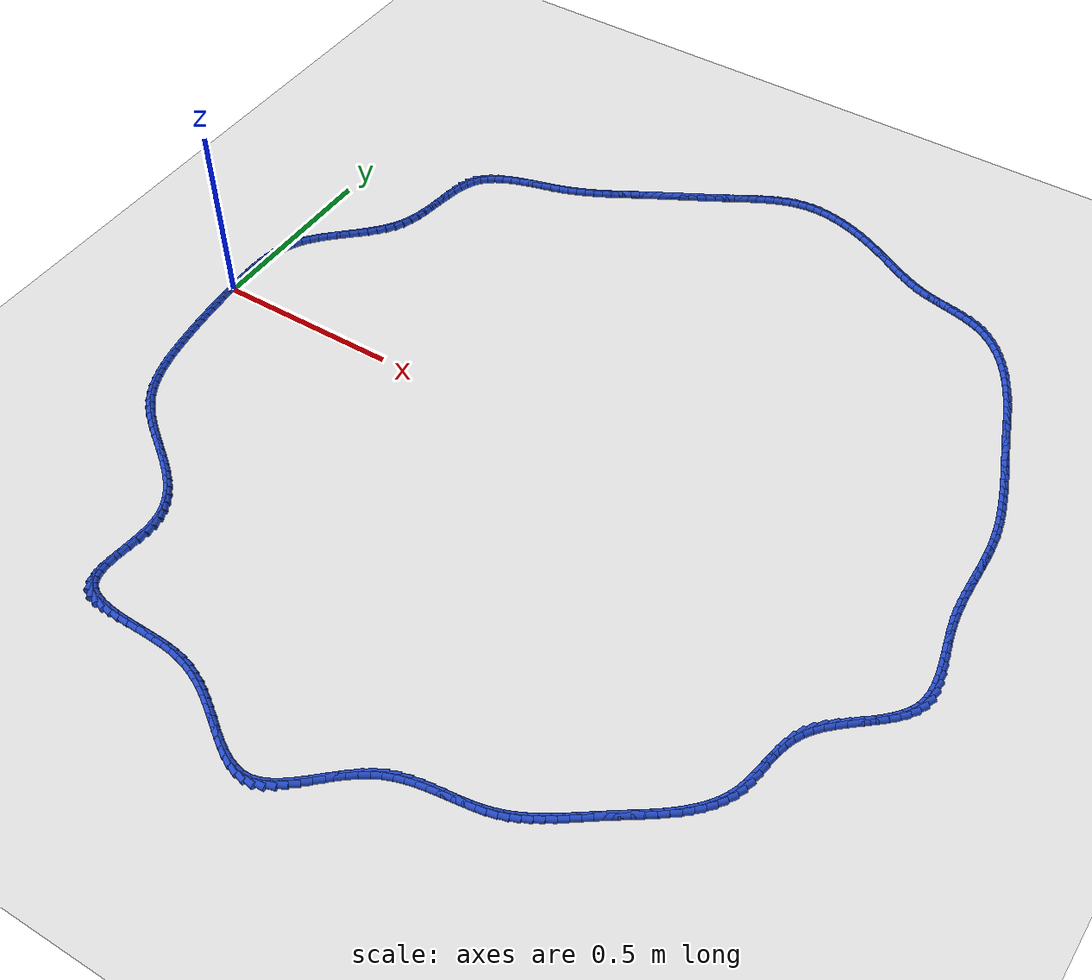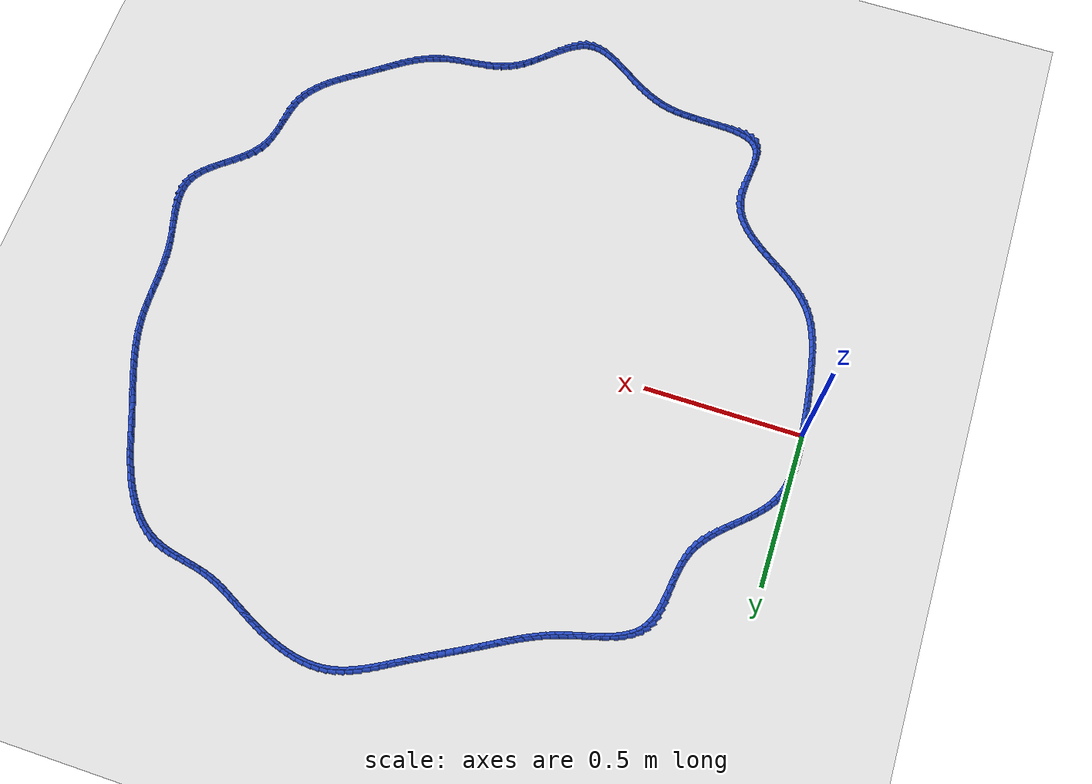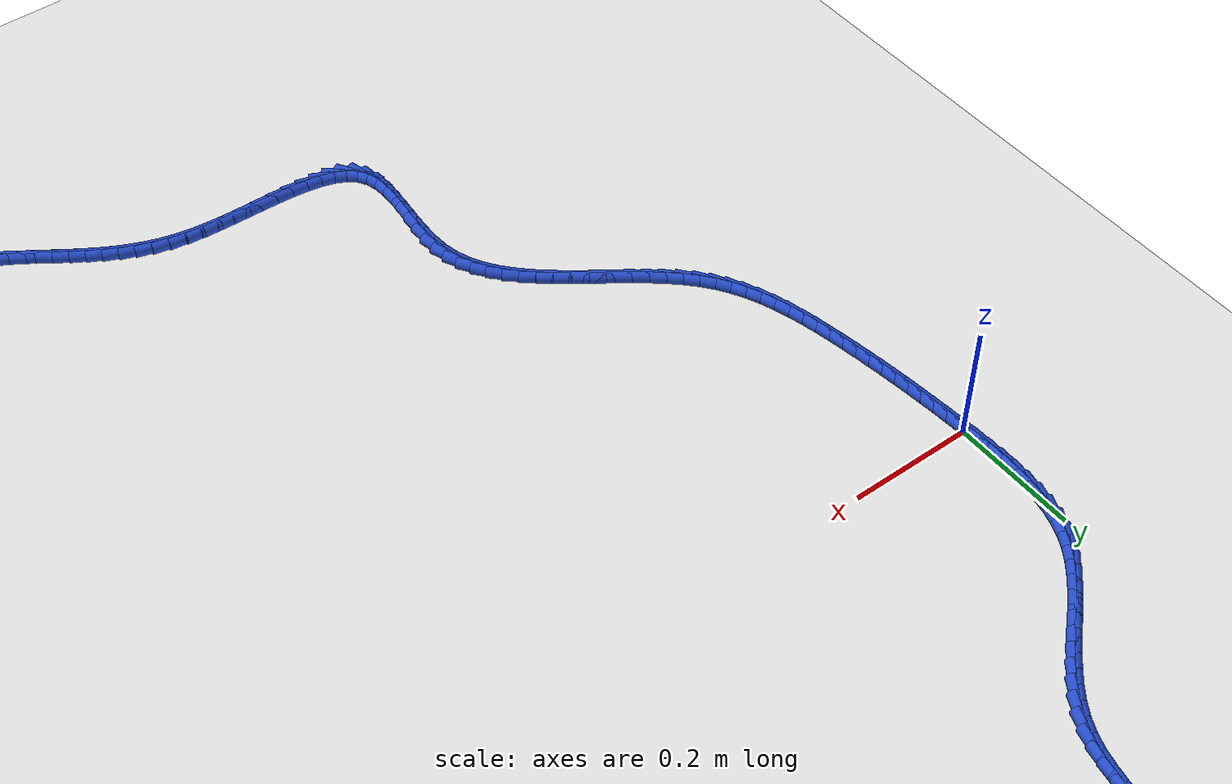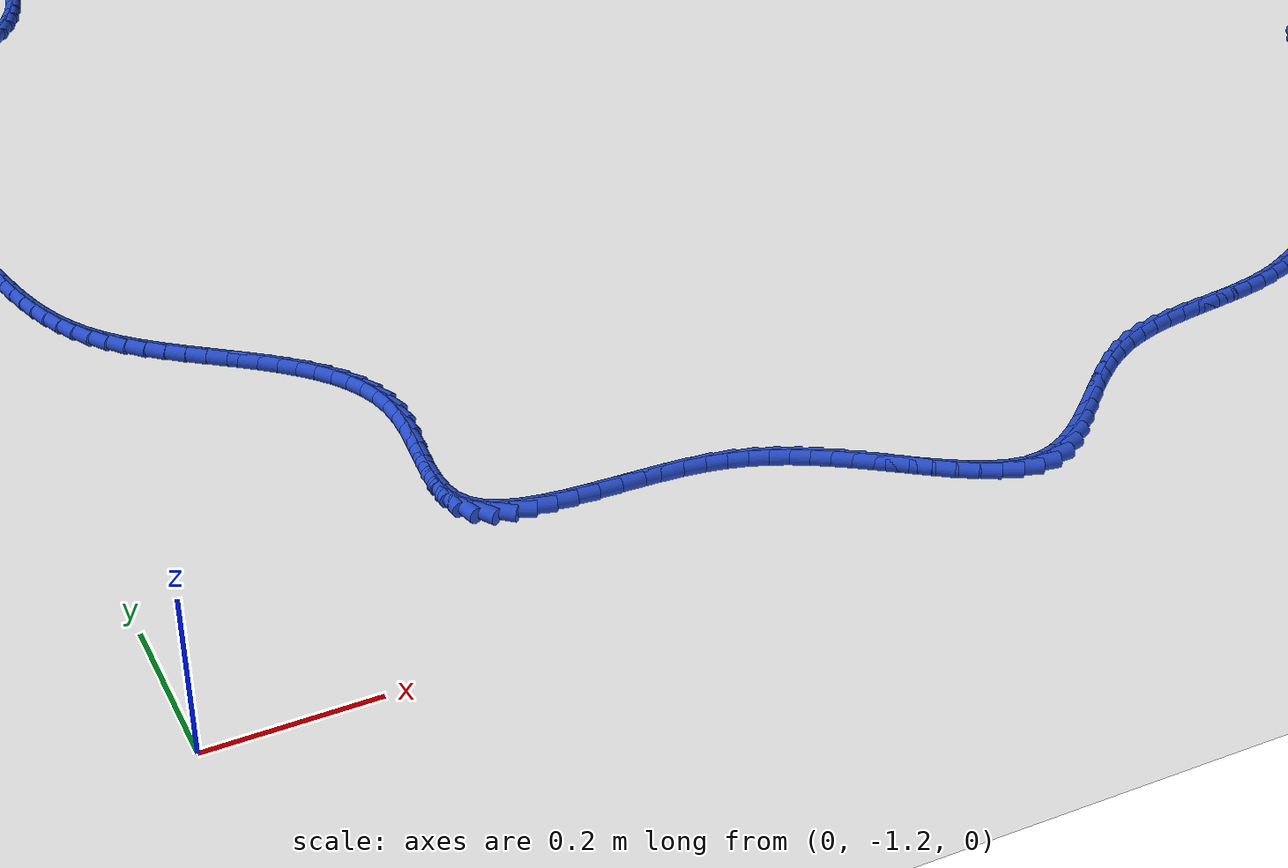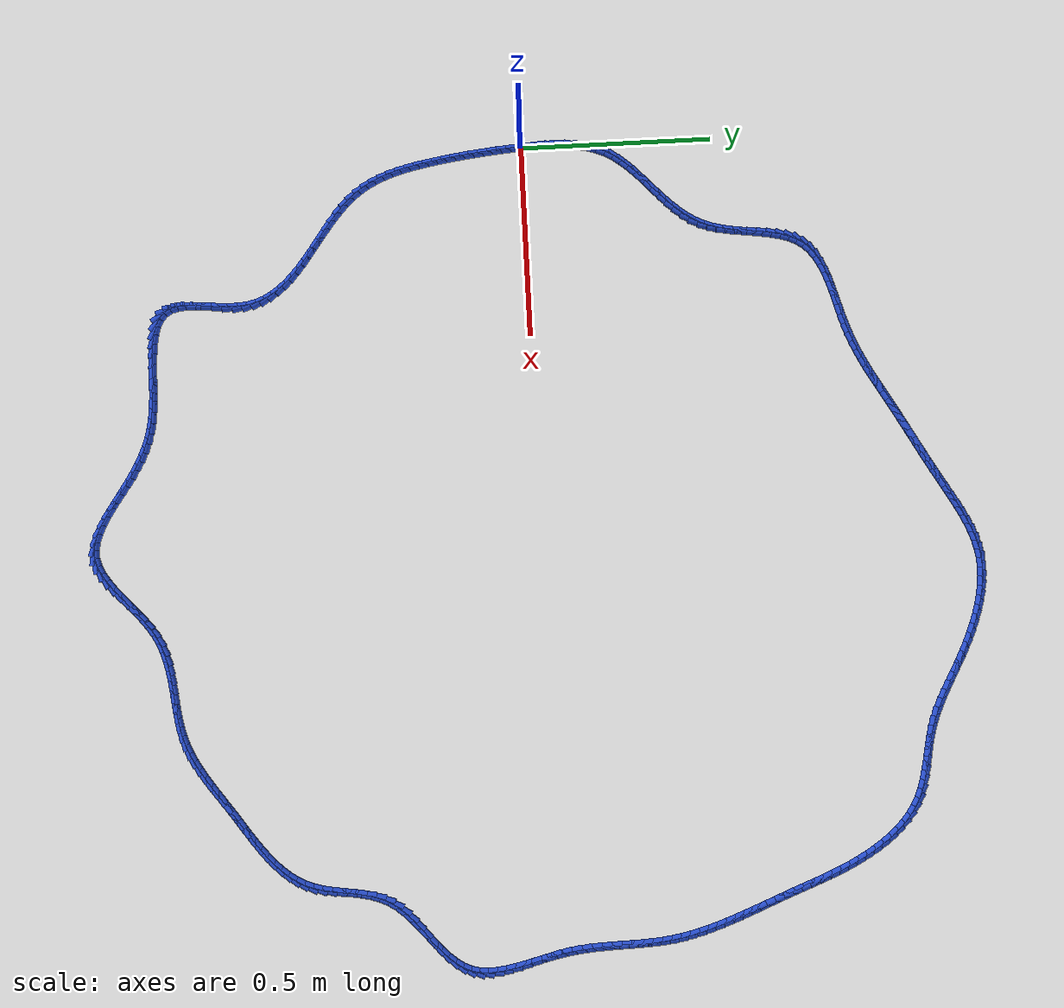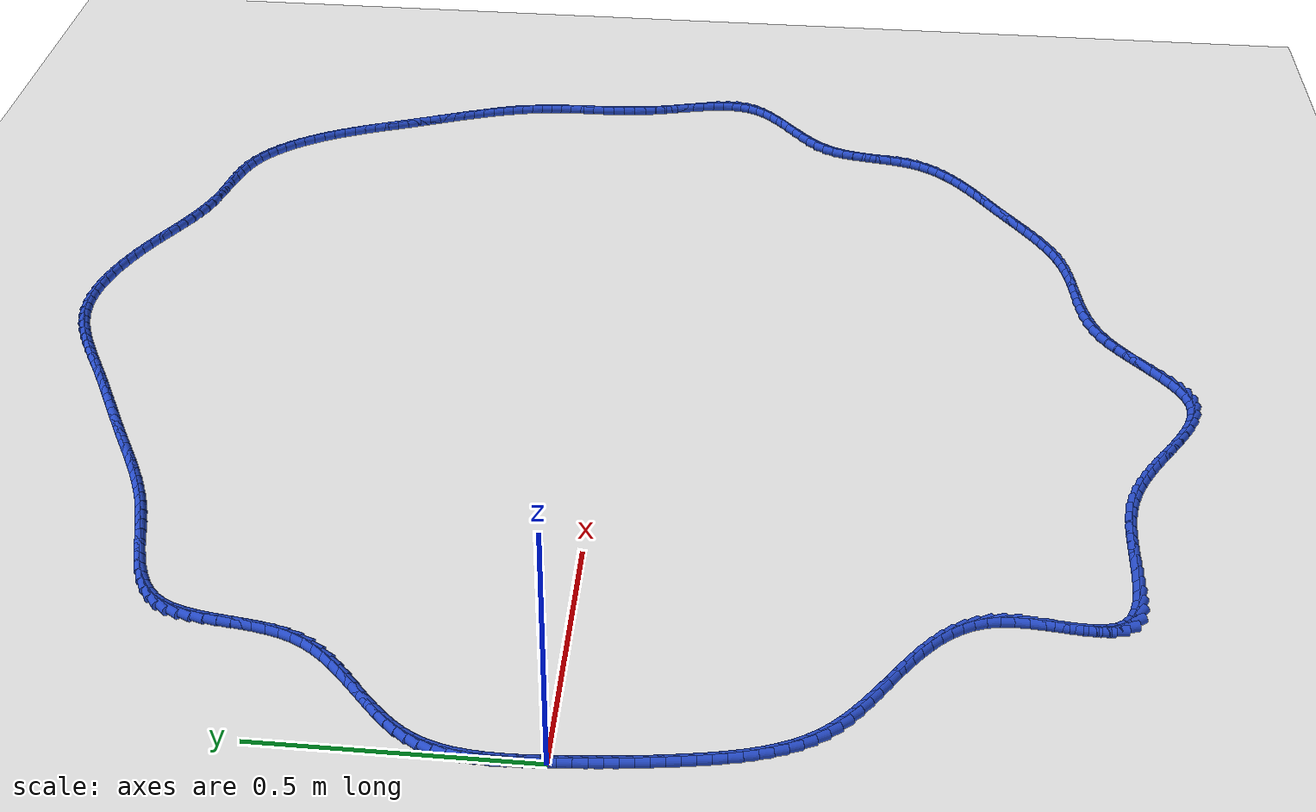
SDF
<sdf version="1.6">
 <world name="default">
  <light name="sun" type="directional">
   <pose>0 0 10 0 -0 0</pose>
   <diffuse>0.8 0.8 0.8 1</diffuse>
   <specular>0.2 0.2 0.2 1</specular>
   <attenuation>
    <range>1000</range>
    <constant>0.9</constant>
    <linear>0.01</linear>
    <quadratic>0.001</quadratic>
   </attenuation>
   <direction>-0.5 0.1 -0.9</direction>
  </light>
  <model name="ground_plane">
   <static>1</static>
   <link name="link">
    <collision name="collision">
     <geometry><plane><normal>0 0 1</normal><size>100 100</size></plane></geometry>
     <surface><friction><ode><mu>100</mu><mu2>50</mu2></ode></friction></surface>
    </collision>
    <visual name="visual">
     <cast_shadows>0</cast_shadows>
     <geometry><plane><normal>0 0 1</normal><size>100 100</size></plane></geometry>
     <material>
      <script><uri>file://media/materials/scripts/gazebo.material</uri><name>Gazebo/WhiteGlow</name></script>
     </material>
    </visual>
   </link>
  </model>
  <gravity>0 0 -9.8</gravity>
  <magnetic_field>6e-06 2.3e-05 -4.2e-05</magnetic_field>
  <atmosphere type="adiabatic"/>
  <physics name="default_physics" default="0" type="ode">
   <max_step_size>0.001</max_step_size>
   <real_time_factor>1</real_time_factor>
   <real_time_update_rate>1000</real_time_update_rate>
  </physics>
  <scene><ambient>0.4 0.4 0.4 1</ambient><background>0.7 0.7 0.7 1</background><shadows>1</shadows></scene>
  <spherical_coordinates>
   <surface_model>EARTH_WGS84</surface_model>
   <latitude_deg>0</latitude_deg>
   <longitude_deg>0</longitude_deg>
   <elevation>0</elevation>
   <heading_deg>0</heading_deg>
  </spherical_coordinates>
  <model name="line">
   <link name="link_0">
    <pose>-2.8189256484623115e-18 1.3877787807814457e-17 0.01 0 1.57 -1.5117144280153771</pose>
    <collision name="collision">
     <geometry><cylinder><radius>0.01</radius><length>0.08</length></cylinder></geometry>
    </collision>
    <visual name="visual">
     <material>
      <script><name>Gazebo/Blue</name><uri>file://media/materials/scripts/gazebo.material</uri></script>
     </material>
     <geometry><cylinder><radius>0.01</radius><length>0.08</length></cylinder></geometry>
    </visual>
   </link>
   <link name="link_1">
    <pose>-0.001506811303396147 0.025474090468086723 0.01 0 1.57 -1.5299592313047388</pose>
    <collision name="collision">
     <geometry><cylinder><radius>0.01</radius><length>0.08</length></cylinder></geometry>
    </collision>
    <visual name="visual">
     <material>
      <script><name>Gazebo/Blue</name><uri>file://media/materials/scripts/gazebo.material</uri></script>
     </material>
     <geometry><cylinder><radius>0.01</radius><length>0.08</length></cylinder></geometry>
    </visual>
   </link>
   <link name="link_2">
    <pose>-0.002555461278012365 0.05113867223505533 0.01 0 1.57 -1.557647988186349</pose>
    <collision name="collision">
     <geometry><cylinder><radius>0.01</radius><length>0.08</length></cylinder></geometry>
    </collision>
    <visual name="visual">
     <material>
      <script><name>Gazebo/Blue</name><uri>file://media/materials/scripts/gazebo.material</uri></script>
     </material>
     <geometry><cylinder><radius>0.01</radius><length>0.08</length></cylinder></geometry>
    </visual>
   </link>
   <link name="link_3">
    <pose>-0.0028930214002868436 0.07681040763593029 0.01 0 1.57 1.546229993007412</pose>
    <collision name="collision">
     <geometry><cylinder><radius>0.01</radius><length>0.08</length></cylinder></geometry>
    </collision>
    <visual name="visual">
     <material>
      <script><name>Gazebo/Blue</name><uri>file://media/materials/scripts/gazebo.material</uri></script>
     </material>
     <geometry><cylinder><radius>0.01</radius><length>0.08</length></cylinder></geometry>
    </visual>
   </link>
   <link name="link_4">
    <pose>-0.002266563146657771 0.10230595900573604 0.01 0 1.57 1.4975902166373434</pose>
    <collision name="collision">
     <geometry><cylinder><radius>0.01</radius><length>0.08</length></cylinder></geometry>
    </collision>
    <visual name="visual">
     <material>
      <script><name>Gazebo/Blue</name><uri>file://media/materials/scripts/gazebo.material</uri></script>
     </material>
     <geometry><cylinder><radius>0.01</radius><length>0.08</length></cylinder></geometry>
    </visual>
   </link>
   <link name="link_5">
    <pose>-0.00042315799356333443 0.12744198867949702 0.01 0 1.57 1.436879056118633</pose>
    <collision name="collision">
     <geometry><cylinder><radius>0.01</radius><length>0.08</length></cylinder></geometry>
    </collision>
    <visual name="visual">
     <material>
      <script><name>Gazebo/Blue</name><uri>file://media/materials/scripts/gazebo.material</uri></script>
     </material>
     <geometry><cylinder><radius>0.01</radius><length>0.08</length></cylinder></geometry>
    </visual>
   </link>
   <link name="link_6">
    <pose>0.0028901225825582813 0.15203515899223768 0.01 0 1.57 1.3628404191255201</pose>
    <collision name="collision">
     <geometry><cylinder><radius>0.01</radius><length>0.08</length></cylinder></geometry>
    </collision>
    <visual name="visual">
     <material>
      <script><name>Gazebo/Blue</name><uri>file://media/materials/scripts/gazebo.material</uri></script>
     </material>
     <geometry><cylinder><radius>0.01</radius><length>0.08</length></cylinder></geometry>
    </visual>
   </link>
   <link name="link_7">
    <pose>0.007926207105268883 0.17590213227898244 0.01 0 1.57 1.2743682834089847</pose>
    <collision name="collision">
     <geometry><cylinder><radius>0.01</radius><length>0.08</length></cylinder></geometry>
    </collision>
    <visual name="visual">
     <material>
      <script><name>Gazebo/Blue</name><uri>file://media/materials/scripts/gazebo.material</uri></script>
     </material>
     <geometry><cylinder><radius>0.01</radius><length>0.08</length></cylinder></geometry>
    </visual>
   </link>
   <link name="link_8">
    <pose>0.01493802409813029 0.19885957087475575 0.01 0 1.57 1.1709403761467672</pose>
    <collision name="collision">
     <geometry><cylinder><radius>0.01</radius><length>0.08</length></cylinder></geometry>
    </collision>
    <visual name="visual">
     <material>
      <script><name>Gazebo/Blue</name><uri>file://media/materials/scripts/gazebo.material</uri></script>
     </material>
     <geometry><cylinder><radius>0.01</radius><length>0.08</length></cylinder></geometry>
    </visual>
   </link>
   <link name="link_9">
    <pose>0.024178502084704293 0.22072413711458208 0.01 0 1.57 1.0573451769031341</pose>
    <collision name="collision">
     <geometry><cylinder><radius>0.01</radius><length>0.08</length></cylinder></geometry>
    </collision>
    <visual name="visual">
     <material>
      <script><name>Gazebo/Blue</name><uri>file://media/materials/scripts/gazebo.material</uri></script>
     </material>
     <geometry><cylinder><radius>0.01</radius><length>0.08</length></cylinder></geometry>
    </visual>
   </link>
   <link name="link_10">
    <pose>0.03581740416147154 0.2413642046069595 0.01 0 1.57 0.9569185156231231</pose>
    <collision name="collision">
     <geometry><cylinder><radius>0.01</radius><length>0.08</length></cylinder></geometry>
    </collision>
    <visual name="visual">
     <material>
      <script><name>Gazebo/Blue</name><uri>file://media/materials/scripts/gazebo.material</uri></script>
     </material>
     <geometry><cylinder><radius>0.01</radius><length>0.08</length></cylinder></geometry>
    </visual>
   </link>
   <link name="link_11">
    <pose>0.04959508432064911 0.26091514843446023 0.01 0 1.57 0.8776598009401864</pose>
    <collision name="collision">
     <geometry><cylinder><radius>0.01</radius><length>0.08</length></cylinder></geometry>
    </collision>
    <visual name="visual">
     <material>
      <script><name>Gazebo/Blue</name><uri>file://media/materials/scripts/gazebo.material</uri></script>
     </material>
     <geometry><cylinder><radius>0.01</radius><length>0.08</length></cylinder></geometry>
    </visual>
   </link>
   <link name="link_12">
    <pose>0.06511370963853909 0.27959826666051685 0.01 0 1.57 0.819053568729166</pose>
    <collision name="collision">
     <geometry><cylinder><radius>0.01</radius><length>0.08</length></cylinder></geometry>
    </collision>
    <visual name="visual">
     <material>
      <script><name>Gazebo/Blue</name><uri>file://media/materials/scripts/gazebo.material</uri></script>
     </material>
     <geometry><cylinder><radius>0.01</radius><length>0.08</length></cylinder></geometry>
    </visual>
   </link>
   <link name="link_13">
    <pose>0.08197538117735292 0.29763489839533874 0.01 0 1.57 0.7798831479889483</pose>
    <collision name="collision">
     <geometry><cylinder><radius>0.01</radius><length>0.08</length></cylinder></geometry>
    </collision>
    <visual name="visual">
     <material>
      <script><name>Gazebo/Blue</name><uri>file://media/materials/scripts/gazebo.material</uri></script>
     </material>
     <geometry><cylinder><radius>0.01</radius><length>0.08</length></cylinder></geometry>
    </visual>
   </link>
   <link name="link_14">
    <pose>0.09978219999930193 0.3152463827491349 0.01 0 1.57 0.7589405536218834</pose>
    <collision name="collision">
     <geometry><cylinder><radius>0.01</radius><length>0.08</length></cylinder></geometry>
    </collision>
    <visual name="visual">
     <material>
      <script><name>Gazebo/Blue</name><uri>file://media/materials/scripts/gazebo.material</uri></script>
     </material>
     <geometry><cylinder><radius>0.01</radius><length>0.08</length></cylinder></geometry>
    </visual>
   </link>
   <link name="link_15">
    <pose>0.11813626716659766 0.33265405883211496 0.01 0 1.57 0.7553973994165484</pose>
    <collision name="collision">
     <geometry><cylinder><radius>0.01</radius><length>0.08</length></cylinder></geometry>
    </collision>
    <visual name="visual">
     <material>
      <script><name>Gazebo/Blue</name><uri>file://media/materials/scripts/gazebo.material</uri></script>
     </material>
     <geometry><cylinder><radius>0.01</radius><length>0.08</length></cylinder></geometry>
    </visual>
   </link>
   <link name="link_16">
    <pose>0.13663968374145144 0.35007926575448783 0.01 0 1.57 0.7689517749209385</pose>
    <collision name="collision">
     <geometry><cylinder><radius>0.01</radius><length>0.08</length></cylinder></geometry>
    </collision>
    <visual name="visual">
     <material>
      <script><name>Gazebo/Blue</name><uri>file://media/materials/scripts/gazebo.material</uri></script>
     </material>
     <geometry><cylinder><radius>0.01</radius><length>0.08</length></cylinder></geometry>
    </visual>
   </link>
   <link name="link_17">
    <pose>0.1548945507860747 0.3677433426264628 0.01 0 1.57 0.7998340010237655</pose>
    <collision name="collision">
     <geometry><cylinder><radius>0.01</radius><length>0.08</length></cylinder></geometry>
    </collision>
    <visual name="visual">
     <material>
      <script><name>Gazebo/Blue</name><uri>file://media/materials/scripts/gazebo.material</uri></script>
     </material>
     <geometry><cylinder><radius>0.01</radius><length>0.08</length></cylinder></geometry>
    </visual>
   </link>
   <link name="link_18">
    <pose>0.17250296936267875 0.3858676285582491 0.01 0 1.57 0.8486940173227783</pose>
    <collision name="collision">
     <geometry><cylinder><radius>0.01</radius><length>0.08</length></cylinder></geometry>
    </collision>
    <visual name="visual">
     <material>
      <script><name>Gazebo/Blue</name><uri>file://media/materials/scripts/gazebo.material</uri></script>
     </material>
     <geometry><cylinder><radius>0.01</radius><length>0.08</length></cylinder></geometry>
    </visual>
   </link>
   <link name="link_19">
    <pose>0.18906704053347528 0.4046734626600561 0.01 0 1.57 0.9163364681718884</pose>
    <collision name="collision">
     <geometry><cylinder><radius>0.01</radius><length>0.08</length></cylinder></geometry>
    </collision>
    <visual name="visual">
     <material>
      <script><name>Gazebo/Blue</name><uri>file://media/materials/scripts/gazebo.material</uri></script>
     </material>
     <geometry><cylinder><radius>0.01</radius><length>0.08</length></cylinder></geometry>
    </visual>
   </link>
   <link name="link_20">
    <pose>0.20418886536067538 0.42438218404209294 0.01 0 1.57 1.0032356528485156</pose>
    <collision name="collision">
     <geometry><cylinder><radius>0.01</radius><length>0.08</length></cylinder></geometry>
    </collision>
    <visual name="visual">
     <material>
      <script><name>Gazebo/Blue</name><uri>file://media/materials/scripts/gazebo.material</uri></script>
     </material>
     <geometry><cylinder><radius>0.01</radius><length>0.08</length></cylinder></geometry>
    </visual>
   </link>
   <link name="link_21">
    <pose>0.21747054490649068 0.44521513181456884 0.01 0 1.57 1.1087956753259751</pose>
    <collision name="collision">
     <geometry><cylinder><radius>0.01</radius><length>0.08</length></cylinder></geometry>
    </collision>
    <visual name="visual">
     <material>
      <script><name>Gazebo/Blue</name><uri>file://media/materials/scripts/gazebo.material</uri></script>
     </material>
     <geometry><cylinder><radius>0.01</radius><length>0.08</length></cylinder></geometry>
    </visual>
   </link>
   <link name="link_22">
    <pose>0.22851418023313252 0.4673936450876931 0.01 0 1.57 1.223546171626963</pose>
    <collision name="collision">
     <geometry><cylinder><radius>0.01</radius><length>0.08</length></cylinder></geometry>
    </collision>
    <visual name="visual">
     <material>
      <script><name>Gazebo/Blue</name><uri>file://media/materials/scripts/gazebo.material</uri></script>
     </material>
     <geometry><cylinder><radius>0.01</radius><length>0.08</length></cylinder></geometry>
    </visual>
   </link>
   <link name="link_23">
    <pose>0.2370727837926084 0.491041725451504 0.01 0 1.57 1.3165023566183214</pose>
    <collision name="collision">
     <geometry><cylinder><radius>0.01</radius><length>0.08</length></cylinder></geometry>
    </collision>
    <visual name="visual">
     <material>
      <script><name>Gazebo/Blue</name><uri>file://media/materials/scripts/gazebo.material</uri></script>
     </material>
     <geometry><cylinder><radius>0.01</radius><length>0.08</length></cylinder></geometry>
    </visual>
   </link>
   <link name="link_24">
    <pose>0.24352819431687692 0.5158777829048992 0.01 0 1.57 1.3820247642812524</pose>
    <collision name="collision">
     <geometry><cylinder><radius>0.01</radius><length>0.08</length></cylinder></geometry>
    </collision>
    <visual name="visual">
     <material>
      <script><name>Gazebo/Blue</name><uri>file://media/materials/scripts/gazebo.material</uri></script>
     </material>
     <geometry><cylinder><radius>0.01</radius><length>0.08</length></cylinder></geometry>
    </visual>
   </link>
   <link name="link_25">
    <pose>0.24842601268147602 0.5415146012181964 0.01 0 1.57 1.4227221613805792</pose>
    <collision name="collision">
     <geometry><cylinder><radius>0.01</radius><length>0.08</length></cylinder></geometry>
    </collision>
    <visual name="visual">
     <material>
      <script><name>Gazebo/Blue</name><uri>file://media/materials/scripts/gazebo.material</uri></script>
     </material>
     <geometry><cylinder><radius>0.01</radius><length>0.08</length></cylinder></geometry>
    </visual>
   </link>
   <link name="link_26">
    <pose>0.25231184015934655 0.5675649639053896 0.01 0 1.57 1.4404102094580056</pose>
    <collision name="collision">
     <geometry><cylinder><radius>0.01</radius><length>0.08</length></cylinder></geometry>
    </collision>
    <visual name="visual">
     <material>
      <script><name>Gazebo/Blue</name><uri>file://media/materials/scripts/gazebo.material</uri></script>
     </material>
     <geometry><cylinder><radius>0.01</radius><length>0.08</length></cylinder></geometry>
    </visual>
   </link>
   <link name="link_27">
    <pose>0.2557312780234293 0.5936416544804726 0.01 0 1.57 1.4355759765988942</pose>
    <collision name="collision">
     <geometry><cylinder><radius>0.01</radius><length>0.08</length></cylinder></geometry>
    </collision>
    <visual name="visual">
     <material>
      <script><name>Gazebo/Blue</name><uri>file://media/materials/scripts/gazebo.material</uri></script>
     </material>
     <geometry><cylinder><radius>0.01</radius><length>0.08</length></cylinder></geometry>
    </visual>
   </link>
   <link name="link_28">
    <pose>0.2592299275466653 0.6193574564574391 0.01 0 1.57 1.4071218423352965</pose>
    <collision name="collision">
     <geometry><cylinder><radius>0.01</radius><length>0.08</length></cylinder></geometry>
    </collision>
    <visual name="visual">
     <material>
      <script><name>Gazebo/Blue</name><uri>file://media/materials/scripts/gazebo.material</uri></script>
     </material>
     <geometry><cylinder><radius>0.01</radius><length>0.08</length></cylinder></geometry>
    </visual>
   </link>
   <link name="link_29">
    <pose>0.26335339000199526 0.6443251533502827 0.01 0 1.57 1.3522156196749635</pose>
    <collision name="collision">
     <geometry><cylinder><radius>0.01</radius><length>0.08</length></cylinder></geometry>
    </collision>
    <visual name="visual">
     <material>
      <script><name>Gazebo/Blue</name><uri>file://media/materials/scripts/gazebo.material</uri></script>
     </material>
     <geometry><cylinder><radius>0.01</radius><length>0.08</length></cylinder></geometry>
    </visual>
   </link>
   <link name="link_30">
    <pose>0.2686472666623604 0.6681575286729979 0.01 0 1.57 1.2663576912355214</pose>
    <collision name="collision">
     <geometry><cylinder><radius>0.01</radius><length>0.08</length></cylinder></geometry>
    </collision>
    <visual name="visual">
     <material>
      <script><name>Gazebo/Blue</name><uri>file://media/materials/scripts/gazebo.material</uri></script>
     </material>
     <geometry><cylinder><radius>0.01</radius><length>0.08</length></cylinder></geometry>
    </visual>
   </link>
   <link name="link_31">
    <pose>0.2756571588007012 0.6904673659395779 0.01 0 1.57 1.1442198601092042</pose>
    <collision name="collision">
     <geometry><cylinder><radius>0.01</radius><length>0.08</length></cylinder></geometry>
    </collision>
    <visual name="visual">
     <material>
      <script><name>Gazebo/Blue</name><uri>file://media/materials/scripts/gazebo.material</uri></script>
     </material>
     <geometry><cylinder><radius>0.01</radius><length>0.08</length></cylinder></geometry>
    </visual>
   </link>
   <link name="link_32">
    <pose>0.2849286676899588 0.7108674486640169 0.01 0 1.57 0.9824461670417258</pose>
    <collision name="collision">
     <geometry><cylinder><radius>0.01</radius><length>0.08</length></cylinder></geometry>
    </collision>
    <visual name="visual">
     <material>
      <script><name>Gazebo/Blue</name><uri>file://media/materials/scripts/gazebo.material</uri></script>
     </material>
     <geometry><cylinder><radius>0.01</radius><length>0.08</length></cylinder></geometry>
    </visual>
   </link>
   <link name="link_33">
    <pose>0.2970068009563321 0.7289710127238102 0.01 0 1.57 0.7990842123239231</pose>
    <collision name="collision">
     <geometry><cylinder><radius>0.01</radius><length>0.08</length></cylinder></geometry>
    </collision>
    <visual name="visual">
     <material>
      <script><name>Gazebo/Blue</name><uri>file://media/materials/scripts/gazebo.material</uri></script>
     </material>
     <geometry><cylinder><radius>0.01</radius><length>0.08</length></cylinder></geometry>
    </visual>
   </link>
   <link name="link_34">
    <pose>0.31219199923927293 0.7445776559701137 0.01 0 1.57 0.6400299945055045</pose>
    <collision name="collision">
     <geometry><cylinder><radius>0.01</radius><length>0.08</length></cylinder></geometry>
    </collision>
    <visual name="visual">
     <material>
      <script><name>Gazebo/Blue</name><uri>file://media/materials/scripts/gazebo.material</uri></script>
     </material>
     <geometry><cylinder><radius>0.01</radius><length>0.08</length></cylinder></geometry>
    </visual>
   </link>
   <link name="link_35">
    <pose>0.33016434578421305 0.7579596934832671 0.01 0 1.57 0.5146574287103698</pose>
    <collision name="collision">
     <geometry><cylinder><radius>0.01</radius><length>0.08</length></cylinder></geometry>
    </collision>
    <visual name="visual">
     <material>
      <script><name>Gazebo/Blue</name><uri>file://media/materials/scripts/gazebo.material</uri></script>
     </material>
     <geometry><cylinder><radius>0.01</radius><length>0.08</length></cylinder></geometry>
    </visual>
   </link>
   <link name="link_36">
    <pose>0.3505070365613898 0.7694632692117985 0.01 0 1.57 0.4205373354107007</pose>
    <collision name="collision">
     <geometry><cylinder><radius>0.01</radius><length>0.08</length></cylinder></geometry>
    </collision>
    <visual name="visual">
     <material>
      <script><name>Gazebo/Blue</name><uri>file://media/materials/scripts/gazebo.material</uri></script>
     </material>
     <geometry><cylinder><radius>0.01</radius><length>0.08</length></cylinder></geometry>
    </visual>
   </link>
   <link name="link_37">
    <pose>0.37280326754104104 0.779434527104236 0.01 0 1.57 0.3531572600027972</pose>
    <collision name="collision">
     <geometry><cylinder><radius>0.01</radius><length>0.08</length></cylinder></geometry>
    </collision>
    <visual name="visual">
     <material>
      <script><name>Gazebo/Blue</name><uri>file://media/materials/scripts/gazebo.material</uri></script>
     </material>
     <geometry><cylinder><radius>0.01</radius><length>0.08</length></cylinder></geometry>
    </visual>
   </link>
   <link name="link_38">
    <pose>0.39663623469340387 0.7882196111091078 0.01 0 1.57 0.3082527455395166</pose>
    <collision name="collision">
     <geometry><cylinder><radius>0.01</radius><length>0.08</length></cylinder></geometry>
    </collision>
    <visual name="visual">
     <material>
      <script><name>Gazebo/Blue</name><uri>file://media/materials/scripts/gazebo.material</uri></script>
     </material>
     <geometry><cylinder><radius>0.01</radius><length>0.08</length></cylinder></geometry>
    </visual>
   </link>
   <link name="link_39">
    <pose>0.42158913398871595 0.7961646651749416 0.01 0 1.57 0.28264999410802977</pose>
    <collision name="collision">
     <geometry><cylinder><radius>0.01</radius><length>0.08</length></cylinder></geometry>
    </collision>
    <visual name="visual">
     <material>
      <script><name>Gazebo/Blue</name><uri>file://media/materials/scripts/gazebo.material</uri></script>
     </material>
     <geometry><cylinder><radius>0.01</radius><length>0.08</length></cylinder></geometry>
    </visual>
   </link>
   <link name="link_40">
    <pose>0.4472451613972146 0.8036158332502654 0.01 0 1.57 0.27442247197472563</pose>
    <collision name="collision">
     <geometry><cylinder><radius>0.01</radius><length>0.08</length></cylinder></geometry>
    </collision>
    <visual name="visual">
     <material>
      <script><name>Gazebo/Blue</name><uri>file://media/materials/scripts/gazebo.material</uri></script>
     </material>
     <geometry><cylinder><radius>0.01</radius><length>0.08</length></cylinder></geometry>
    </visual>
   </link>
   <link name="link_41">
    <pose>0.4731875128891375 0.8109192592836074 0.01 0 1.57 0.2828428707488643</pose>
    <collision name="collision">
     <geometry><cylinder><radius>0.01</radius><length>0.08</length></cylinder></geometry>
    </collision>
    <visual name="visual">
     <material>
      <script><name>Gazebo/Blue</name><uri>file://media/materials/scripts/gazebo.material</uri></script>
     </material>
     <geometry><cylinder><radius>0.01</radius><length>0.08</length></cylinder></geometry>
    </visual>
   </link>
   <link name="link_42">
    <pose>0.498999384434722 0.8184210872234958 0.01 0 1.57 0.3083274060708118</pose>
    <collision name="collision">
     <geometry><cylinder><radius>0.01</radius><length>0.08</length></cylinder></geometry>
    </collision>
    <visual name="visual">
     <material>
      <script><name>Gazebo/Blue</name><uri>file://media/materials/scripts/gazebo.material</uri></script>
     </material>
     <geometry><cylinder><radius>0.01</radius><length>0.08</length></cylinder></geometry>
    </visual>
   </link>
   <link name="link_43">
    <pose>0.5242639720042056 0.8264674610184584 0.01 0 1.57 0.34894729370363314</pose>
    <collision name="collision">
     <geometry><cylinder><radius>0.01</radius><length>0.08</length></cylinder></geometry>
    </collision>
    <visual name="visual">
     <material>
      <script><name>Gazebo/Blue</name><uri>file://media/materials/scripts/gazebo.material</uri></script>
     </material>
     <geometry><cylinder><radius>0.01</radius><length>0.08</length></cylinder></geometry>
    </visual>
   </link>
   <link name="link_44">
    <pose>0.5486432866751864 0.835337532806083 0.01 0 1.57 0.3900678773051173</pose>
    <collision name="collision">
     <geometry><cylinder><radius>0.01</radius><length>0.08</length></cylinder></geometry>
    </collision>
    <visual name="visual">
     <material>
      <script><name>Gazebo/Blue</name><uri>file://media/materials/scripts/gazebo.material</uri></script>
     </material>
     <geometry><cylinder><radius>0.01</radius><length>0.08</length></cylinder></geometry>
    </visual>
   </link>
   <link name="link_45">
    <pose>0.5721582861386475 0.8450053547949373 0.01 0 1.57 0.4266675276720539</pose>
    <collision name="collision">
     <geometry><cylinder><radius>0.01</radius><length>0.08</length></cylinder></geometry>
    </collision>
    <visual name="visual">
     <material>
      <script><name>Gazebo/Blue</name><uri>file://media/materials/scripts/gazebo.material</uri></script>
     </material>
     <geometry><cylinder><radius>0.01</radius><length>0.08</length></cylinder></geometry>
    </visual>
   </link>
   <link name="link_46">
    <pose>0.5949320585295944 0.8553581696512762 0.01 0 1.57 0.45811593838444686</pose>
    <collision name="collision">
     <geometry><cylinder><radius>0.01</radius><length>0.08</length></cylinder></geometry>
    </collision>
    <visual name="visual">
     <material>
      <script><name>Gazebo/Blue</name><uri>file://media/materials/scripts/gazebo.material</uri></script>
     </material>
     <geometry><cylinder><radius>0.01</radius><length>0.08</length></cylinder></geometry>
    </visual>
   </link>
   <link name="link_47">
    <pose>0.6170876992434116 0.8662832138701294 0.01 0 1.57 0.4839062602346822</pose>
    <collision name="collision">
     <geometry><cylinder><radius>0.01</radius><length>0.08</length></cylinder></geometry>
    </collision>
    <visual name="visual">
     <material>
      <script><name>Gazebo/Blue</name><uri>file://media/materials/scripts/gazebo.material</uri></script>
     </material>
     <geometry><cylinder><radius>0.01</radius><length>0.08</length></cylinder></geometry>
    </visual>
   </link>
   <link name="link_48">
    <pose>0.6387483036754833 0.8776677239465248 0.01 0 1.57 0.5036523962917425</pose>
    <collision name="collision">
     <geometry><cylinder><radius>0.01</radius><length>0.08</length></cylinder></geometry>
    </collision>
    <visual name="visual">
     <material>
      <script><name>Gazebo/Blue</name><uri>file://media/materials/scripts/gazebo.material</uri></script>
     </material>
     <geometry><cylinder><radius>0.01</radius><length>0.08</length></cylinder></geometry>
    </visual>
   </link>
   <link name="link_49">
    <pose>0.660036967221194 0.8893989363754918 0.01 0 1.57 0.5170798331639326</pose>
    <collision name="collision">
     <geometry><cylinder><radius>0.01</radius><length>0.08</length></cylinder></geometry>
    </collision>
    <visual name="visual">
     <material>
      <script><name>Gazebo/Blue</name><uri>file://media/materials/scripts/gazebo.material</uri></script>
     </material>
     <geometry><cylinder><radius>0.01</radius><length>0.08</length></cylinder></geometry>
    </visual>
   </link>
   <link name="link_50">
    <pose>0.681076785275928 0.9013640876520587 0.01 0 1.57 0.5240140848626647</pose>
    <collision name="collision">
     <geometry><cylinder><radius>0.01</radius><length>0.08</length></cylinder></geometry>
    </collision>
    <visual name="visual">
     <material>
      <script><name>Gazebo/Blue</name><uri>file://media/materials/scripts/gazebo.material</uri></script>
     </material>
     <geometry><cylinder><radius>0.01</radius><length>0.08</length></cylinder></geometry>
    </visual>
   </link>
   <link name="link_51">
    <pose>0.7019908532350694 0.9134504142712542 0.01 0 1.57 0.5243705593597168</pose>
    <collision name="collision">
     <geometry><cylinder><radius>0.01</radius><length>0.08</length></cylinder></geometry>
    </collision>
    <visual name="visual">
     <material>
      <script><name>Gazebo/Blue</name><uri>file://media/materials/scripts/gazebo.material</uri></script>
     </material>
     <geometry><cylinder><radius>0.01</radius><length>0.08</length></cylinder></geometry>
    </visual>
   </link>
   <link name="link_52">
    <pose>0.7229022664940031 0.9255451527281076 0.01 0 1.57 0.5189736775174607</pose>
    <collision name="collision">
     <geometry><cylinder><radius>0.01</radius><length>0.08</length></cylinder></geometry>
    </collision>
    <visual name="visual">
     <material>
      <script><name>Gazebo/Blue</name><uri>file://media/materials/scripts/gazebo.material</uri></script>
     </material>
     <geometry><cylinder><radius>0.01</radius><length>0.08</length></cylinder></geometry>
    </visual>
   </link>
   <link name="link_53">
    <pose>0.7439206881929213 0.9375508720784255 0.01 0 1.57 0.5131259821484414</pose>
    <collision name="collision">
     <geometry><cylinder><radius>0.01</radius><length>0.08</length></cylinder></geometry>
    </collision>
    <visual name="visual">
     <material>
      <script><name>Gazebo/Blue</name><uri>file://media/materials/scripts/gazebo.material</uri></script>
     </material>
     <geometry><cylinder><radius>0.01</radius><length>0.08</length></cylinder></geometry>
    </visual>
   </link>
   <link name="link_54">
    <pose>0.7650701082723669 0.9494679350486956 0.01 0 1.57 0.5088966237593365</pose>
    <collision name="collision">
     <geometry><cylinder><radius>0.01</radius><length>0.08</length></cylinder></geometry>
    </collision>
    <visual name="visual">
     <material>
      <script><name>Gazebo/Blue</name><uri>file://media/materials/scripts/gazebo.material</uri></script>
     </material>
     <geometry><cylinder><radius>0.01</radius><length>0.08</length></cylinder></geometry>
    </visual>
   </link>
   <link name="link_55">
    <pose>0.7863408606031678 0.9613351218706637 0.01 0 1.57 0.5062799331284847</pose>
    <collision name="collision">
     <geometry><cylinder><radius>0.01</radius><length>0.08</length></cylinder></geometry>
    </collision>
    <visual name="visual">
     <material>
      <script><name>Gazebo/Blue</name><uri>file://media/materials/scripts/gazebo.material</uri></script>
     </material>
     <geometry><cylinder><radius>0.01</radius><length>0.08</length></cylinder></geometry>
    </visual>
   </link>
   <link name="link_56">
    <pose>0.8077231990660553 0.9731913040826359 0.01 0 1.57 0.5052611219251432</pose>
    <collision name="collision">
     <geometry><cylinder><radius>0.01</radius><length>0.08</length></cylinder></geometry>
    </collision>
    <visual name="visual">
     <material>
      <script><name>Gazebo/Blue</name><uri>file://media/materials/scripts/gazebo.material</uri></script>
     </material>
     <geometry><cylinder><radius>0.01</radius><length>0.08</length></cylinder></geometry>
    </visual>
   </link>
   <link name="link_57">
    <pose>0.8292073775417609 0.9850753532229184 0.01 0 1.57 0.5058215385313971</pose>
    <collision name="collision">
     <geometry><cylinder><radius>0.01</radius><length>0.08</length></cylinder></geometry>
    </collision>
    <visual name="visual">
     <material>
      <script><name>Gazebo/Blue</name><uri>file://media/materials/scripts/gazebo.material</uri></script>
     </material>
     <geometry><cylinder><radius>0.01</radius><length>0.08</length></cylinder></geometry>
    </visual>
   </link>
   <link name="link_58">
    <pose>0.8507836499110153 0.9970261408298173 0.01 0 1.57 0.5079389028882587</pose>
    <collision name="collision">
     <geometry><cylinder><radius>0.01</radius><length>0.08</length></cylinder></geometry>
    </collision>
    <visual name="visual">
     <material>
      <script><name>Gazebo/Blue</name><uri>file://media/materials/scripts/gazebo.material</uri></script>
     </material>
     <geometry><cylinder><radius>0.01</radius><length>0.08</length></cylinder></geometry>
    </visual>
   </link>
   <link name="link_59">
    <pose>0.8724422700545508 1.0090825384416393 0.01 0 1.57 0.5115874414179808</pose>
    <collision name="collision">
     <geometry><cylinder><radius>0.01</radius><length>0.08</length></cylinder></geometry>
    </collision>
    <visual name="visual">
     <material>
      <script><name>Gazebo/Blue</name><uri>file://media/materials/scripts/gazebo.material</uri></script>
     </material>
     <geometry><cylinder><radius>0.01</radius><length>0.08</length></cylinder></geometry>
    </visual>
   </link>
   <link name="link_60">
    <pose>0.8941734918530978 1.02128341759669 0.01 0 1.57 0.5167379319178707</pose>
    <collision name="collision">
     <geometry><cylinder><radius>0.01</radius><length>0.08</length></cylinder></geometry>
    </collision>
    <visual name="visual">
     <material>
      <script><name>Gazebo/Blue</name><uri>file://media/materials/scripts/gazebo.material</uri></script>
     </material>
     <geometry><cylinder><radius>0.01</radius><length>0.08</length></cylinder></geometry>
    </visual>
   </link>
   <link name="link_61">
    <pose>0.9159675691873881 1.033667649833276 0.01 0 1.57 0.5233528952993878</pose>
    <collision name="collision">
     <geometry><cylinder><radius>0.01</radius><length>0.08</length></cylinder></geometry>
    </collision>
    <visual name="visual">
     <material>
      <script><name>Gazebo/Blue</name><uri>file://media/materials/scripts/gazebo.material</uri></script>
     </material>
     <geometry><cylinder><radius>0.01</radius><length>0.08</length></cylinder></geometry>
    </visual>
   </link>
   <link name="link_62">
    <pose>0.937814773648279 1.046273977830073 0.01 0 1.57 0.5283934004789227</pose>
    <collision name="collision">
     <geometry><cylinder><radius>0.01</radius><length>0.08</length></cylinder></geometry>
    </collision>
    <visual name="visual">
     <material>
      <script><name>Gazebo/Blue</name><uri>file://media/materials/scripts/gazebo.material</uri></script>
     </material>
     <geometry><cylinder><radius>0.01</radius><length>0.08</length></cylinder></geometry>
    </visual>
   </link>
   <link name="link_63">
    <pose>0.959716609713695 1.0590594133029685 0.01 0 1.57 0.5237648150838516</pose>
    <collision name="collision">
     <geometry><cylinder><radius>0.01</radius><length>0.08</length></cylinder></geometry>
    </collision>
    <visual name="visual">
     <material>
      <script><name>Gazebo/Blue</name><uri>file://media/materials/scripts/gazebo.material</uri></script>
     </material>
     <geometry><cylinder><radius>0.01</radius><length>0.08</length></cylinder></geometry>
    </visual>
   </link>
   <link name="link_64">
    <pose>0.9817050457827852 1.0717593111847443 0.01 0 1.57 0.5080652768700663</pose>
    <collision name="collision">
     <geometry><cylinder><radius>0.01</radius><length>0.08</length></cylinder></geometry>
    </collision>
    <visual name="visual">
     <material>
      <script><name>Gazebo/Blue</name><uri>file://media/materials/scripts/gazebo.material</uri></script>
     </material>
     <geometry><cylinder><radius>0.01</radius><length>0.08</length></cylinder></geometry>
    </visual>
   </link>
   <link name="link_65">
    <pose>1.003817164879171 1.0840718121835666 0.01 0 1.57 0.48097935337884307</pose>
    <collision name="collision">
     <geometry><cylinder><radius>0.01</radius><length>0.08</length></cylinder></geometry>
    </collision>
    <visual name="visual">
     <material>
      <script><name>Gazebo/Blue</name><uri>file://media/materials/scripts/gazebo.material</uri></script>
     </material>
     <geometry><cylinder><radius>0.01</radius><length>0.08</length></cylinder></geometry>
    </visual>
   </link>
   <link name="link_66">
    <pose>1.0260900500264734 1.0956950570076012 0.01 0 1.57 0.44194150988343367</pose>
    <collision name="collision">
     <geometry><cylinder><radius>0.01</radius><length>0.08</length></cylinder></geometry>
    </collision>
    <visual name="visual">
     <material>
      <script><name>Gazebo/Blue</name><uri>file://media/materials/scripts/gazebo.material</uri></script>
     </material>
     <geometry><cylinder><radius>0.01</radius><length>0.08</length></cylinder></geometry>
    </visual>
   </link>
   <link name="link_67">
    <pose>1.0485607842483144 1.106327186365014 0.01 0 1.57 0.3902214711271216</pose>
    <collision name="collision">
     <geometry><cylinder><radius>0.01</radius><length>0.08</length></cylinder></geometry>
    </collision>
    <visual name="visual">
     <material>
      <script><name>Gazebo/Blue</name><uri>file://media/materials/scripts/gazebo.material</uri></script>
     </material>
     <geometry><cylinder><radius>0.01</radius><length>0.08</length></cylinder></geometry>
    </visual>
   </link>
   <link name="link_68">
    <pose>1.0712664505683156 1.1156663409639707 0.01 0 1.57 0.3250798193167384</pose>
    <collision name="collision">
     <geometry><cylinder><radius>0.01</radius><length>0.08</length></cylinder></geometry>
    </collision>
    <visual name="visual">
     <material>
      <script><name>Gazebo/Blue</name><uri>file://media/materials/scripts/gazebo.material</uri></script>
     </material>
     <geometry><cylinder><radius>0.01</radius><length>0.08</length></cylinder></geometry>
    </visual>
   </link>
   <link name="link_69">
    <pose>1.0942441320100968 1.1234106615126367 0.01 0 1.57 0.24602648844768754</pose>
    <collision name="collision">
     <geometry><cylinder><radius>0.01</radius><length>0.08</length></cylinder></geometry>
    </collision>
    <visual name="visual">
     <material>
      <script><name>Gazebo/Blue</name><uri>file://media/materials/scripts/gazebo.material</uri></script>
     </material>
     <geometry><cylinder><radius>0.01</radius><length>0.08</length></cylinder></geometry>
    </visual>
   </link>
   <link name="link_70">
    <pose>1.1175309115972816 1.1292582887191789 0.01 0 1.57 0.15348852929266052</pose>
    <collision name="collision">
     <geometry><cylinder><radius>0.01</radius><length>0.08</length></cylinder></geometry>
    </collision>
    <visual name="visual">
     <material>
      <script><name>Gazebo/Blue</name><uri>file://media/materials/scripts/gazebo.material</uri></script>
     </material>
     <geometry><cylinder><radius>0.01</radius><length>0.08</length></cylinder></geometry>
    </visual>
   </link>
   <link name="link_71">
    <pose>1.1411621309180935 1.132914164269768 0.01 0 1.57 0.05758001351447266</pose>
    <collision name="collision">
     <geometry><cylinder><radius>0.01</radius><length>0.08</length></cylinder></geometry>
    </collision>
    <visual name="visual">
     <material>
      <script><name>Gazebo/Blue</name><uri>file://media/materials/scripts/gazebo.material</uri></script>
     </material>
     <geometry><cylinder><radius>0.01</radius><length>0.08</length></cylinder></geometry>
    </visual>
   </link>
   <link name="link_72">
    <pose>1.1651188755700714 1.1342951204554188 0.01 0 1.57 -0.030110901097796038</pose>
    <collision name="collision">
     <geometry><cylinder><radius>0.01</radius><length>0.08</length></cylinder></geometry>
    </collision>
    <visual name="visual">
     <material>
      <script><name>Gazebo/Blue</name><uri>file://media/materials/scripts/gazebo.material</uri></script>
     </material>
     <geometry><cylinder><radius>0.01</radius><length>0.08</length></cylinder></geometry>
    </visual>
   </link>
   <link name="link_73">
    <pose>1.1893186694531075 1.1335662225528327 0.01 0 1.57 -0.10876103123228287</pose>
    <collision name="collision">
     <geometry><cylinder><radius>0.01</radius><length>0.08</length></cylinder></geometry>
    </collision>
    <visual name="visual">
     <material>
      <script><name>Gazebo/Blue</name><uri>file://media/materials/scripts/gazebo.material</uri></script>
     </material>
     <geometry><cylinder><radius>0.01</radius><length>0.08</length></cylinder></geometry>
    </visual>
   </link>
   <link name="link_74">
    <pose>1.2136754192585035 1.1309066624357098 0.01 0 1.57 -0.17865040572887414</pose>
    <collision name="collision">
     <geometry><cylinder><radius>0.01</radius><length>0.08</length></cylinder></geometry>
    </collision>
    <visual name="visual">
     <material>
      <script><name>Gazebo/Blue</name><uri>file://media/materials/scripts/gazebo.material</uri></script>
     </material>
     <geometry><cylinder><radius>0.01</radius><length>0.08</length></cylinder></geometry>
    </visual>
   </link>
   <link name="link_75">
    <pose>1.2381030316775643 1.1264956319777528 0.01 0 1.57 -0.24035519986137915</pose>
    <collision name="collision">
     <geometry><cylinder><radius>0.01</radius><length>0.08</length></cylinder></geometry>
    </collision>
    <visual name="visual">
     <material>
      <script><name>Gazebo/Blue</name><uri>file://media/materials/scripts/gazebo.material</uri></script>
     </material>
     <geometry><cylinder><radius>0.01</radius><length>0.08</length></cylinder></geometry>
    </visual>
   </link>
   <link name="link_76">
    <pose>1.262515413401593 1.1205123230526615 0.01 0 1.57 -0.29458897683144164</pose>
    <collision name="collision">
     <geometry><cylinder><radius>0.01</radius><length>0.08</length></cylinder></geometry>
    </collision>
    <visual name="visual">
     <material>
      <script><name>Gazebo/Blue</name><uri>file://media/materials/scripts/gazebo.material</uri></script>
     </material>
     <geometry><cylinder><radius>0.01</radius><length>0.08</length></cylinder></geometry>
    </visual>
   </link>
   <link name="link_77">
    <pose>1.2868264711218944 1.1131359275341384 0.01 0 1.57 -0.3420936673481005</pose>
    <collision name="collision">
     <geometry><cylinder><radius>0.01</radius><length>0.08</length></cylinder></geometry>
    </collision>
    <visual name="visual">
     <material>
      <script><name>Gazebo/Blue</name><uri>file://media/materials/scripts/gazebo.material</uri></script>
     </material>
     <geometry><cylinder><radius>0.01</radius><length>0.08</length></cylinder></geometry>
    </visual>
   </link>
   <link name="link_78">
    <pose>1.310950111529771 1.1045456372958835 0.01 0 1.57 -0.3835728216554698</pose>
    <collision name="collision">
     <geometry><cylinder><radius>0.01</radius><length>0.08</length></cylinder></geometry>
    </collision>
    <visual name="visual">
     <material>
      <script><name>Gazebo/Blue</name><uri>file://media/materials/scripts/gazebo.material</uri></script>
     </material>
     <geometry><cylinder><radius>0.01</radius><length>0.08</length></cylinder></geometry>
    </visual>
   </link>
   <link name="link_79">
    <pose>1.3348002413165274 1.0949206442115993 0.01 0 1.57 -0.41965496621604886</pose>
    <collision name="collision">
     <geometry><cylinder><radius>0.01</radius><length>0.08</length></cylinder></geometry>
    </collision>
    <visual name="visual">
     <material>
      <script><name>Gazebo/Blue</name><uri>file://media/materials/scripts/gazebo.material</uri></script>
     </material>
     <geometry><cylinder><radius>0.01</radius><length>0.08</length></cylinder></geometry>
    </visual>
   </link>
   <link name="link_80">
    <pose>1.3582907671734672 1.084440140154987 0.01 0 1.57 -0.4508757748941615</pose>
    <collision name="collision">
     <geometry><cylinder><radius>0.01</radius><length>0.08</length></cylinder></geometry>
    </collision>
    <visual name="visual">
     <material>
      <script><name>Gazebo/Blue</name><uri>file://media/materials/scripts/gazebo.material</uri></script>
     </material>
     <geometry><cylinder><radius>0.01</radius><length>0.08</length></cylinder></geometry>
    </visual>
   </link>
   <link name="link_81">
    <pose>1.3813355957918936 1.0732833169997473 0.01 0 1.57 -0.47716823262782676</pose>
    <collision name="collision">
     <geometry><cylinder><radius>0.01</radius><length>0.08</length></cylinder></geometry>
    </collision>
    <visual name="visual">
     <material>
      <script><name>Gazebo/Blue</name><uri>file://media/materials/scripts/gazebo.material</uri></script>
     </material>
     <geometry><cylinder><radius>0.01</radius><length>0.08</length></cylinder></geometry>
    </visual>
   </link>
   <link name="link_82">
    <pose>1.4038682327131033 1.0616335639073884 0.01 0 1.57 -0.4948079234408876</pose>
    <collision name="collision">
     <geometry><cylinder><radius>0.01</radius><length>0.08</length></cylinder></geometry>
    </collision>
    <visual name="visual">
     <material>
      <script><name>Gazebo/Blue</name><uri>file://media/materials/scripts/gazebo.material</uri></script>
     </material>
     <geometry><cylinder><radius>0.01</radius><length>0.08</length></cylinder></geometry>
    </visual>
   </link>
   <link name="link_83">
    <pose>1.4259726121689777 1.049706485833155 0.01 0 1.57 -0.5017004527025022</pose>
    <collision name="collision">
     <geometry><cylinder><radius>0.01</radius><length>0.08</length></cylinder></geometry>
    </collision>
    <visual name="visual">
     <material>
      <script><name>Gazebo/Blue</name><uri>file://media/materials/scripts/gazebo.material</uri></script>
     </material>
     <geometry><cylinder><radius>0.01</radius><length>0.08</length></cylinder></geometry>
    </visual>
   </link>
   <link name="link_84">
    <pose>1.4478023384665428 1.037732608268805 0.01 0 1.57 -0.4975260520369259</pose>
    <collision name="collision">
     <geometry><cylinder><radius>0.01</radius><length>0.08</length></cylinder></geometry>
    </collision>
    <visual name="visual">
     <material>
      <script><name>Gazebo/Blue</name><uri>file://media/materials/scripts/gazebo.material</uri></script>
     </material>
     <geometry><cylinder><radius>0.01</radius><length>0.08</length></cylinder></geometry>
    </visual>
   </link>
   <link name="link_85">
    <pose>1.469511395687868 1.0259425380386813 0.01 0 1.57 -0.48203657769170266</pose>
    <collision name="collision">
     <geometry><cylinder><radius>0.01</radius><length>0.08</length></cylinder></geometry>
    </collision>
    <visual name="visual">
     <material>
      <script><name>Gazebo/Blue</name><uri>file://media/materials/scripts/gazebo.material</uri></script>
     </material>
     <geometry><cylinder><radius>0.01</radius><length>0.08</length></cylinder></geometry>
    </visual>
   </link>
   <link name="link_86">
    <pose>1.4912537679150244 1.0145668819671279 0.01 0 1.57 -0.45506746914877116</pose>
    <collision name="collision">
     <geometry><cylinder><radius>0.01</radius><length>0.08</length></cylinder></geometry>
    </collision>
    <visual name="visual">
     <material>
      <script><name>Gazebo/Blue</name><uri>file://media/materials/scripts/gazebo.material</uri></script>
     </material>
     <geometry><cylinder><radius>0.01</radius><length>0.08</length></cylinder></geometry>
    </visual>
   </link>
   <link name="link_87">
    <pose>1.5131834392300825 1.0038362468784885 0.01 0 1.57 -0.4166035745356155</pose>
    <collision name="collision">
     <geometry><cylinder><radius>0.01</radius><length>0.08</length></cylinder></geometry>
    </collision>
    <visual name="visual">
     <material>
      <script><name>Gazebo/Blue</name><uri>file://media/materials/scripts/gazebo.material</uri></script>
     </material>
     <geometry><cylinder><radius>0.01</radius><length>0.08</length></cylinder></geometry>
    </visual>
   </link>
   <link name="link_88">
    <pose>1.5354543937151124 0.9939812395971076 0.01 0 1.57 -0.36688810264493504</pose>
    <collision name="collision">
     <geometry><cylinder><radius>0.01</radius><length>0.08</length></cylinder></geometry>
    </collision>
    <visual name="visual">
     <material>
      <script><name>Gazebo/Blue</name><uri>file://media/materials/scripts/gazebo.material</uri></script>
     </material>
     <geometry><cylinder><radius>0.01</radius><length>0.08</length></cylinder></geometry>
    </visual>
   </link>
   <link name="link_89">
    <pose>1.5582206154521852 0.9852324669473287 0.01 0 1.57 -0.3068984192505896</pose>
    <collision name="collision">
     <geometry><cylinder><radius>0.01</radius><length>0.08</length></cylinder></geometry>
    </collision>
    <visual name="visual">
     <material>
      <script><name>Gazebo/Blue</name><uri>file://media/materials/scripts/gazebo.material</uri></script>
     </material>
     <geometry><cylinder><radius>0.01</radius><length>0.08</length></cylinder></geometry>
    </visual>
   </link>
   <link name="link_90">
    <pose>1.5816319221640303 0.9778131650292858 0.01 0 1.57 -0.25119528374120437</pose>
    <collision name="collision">
     <geometry><cylinder><radius>0.01</radius><length>0.08</length></cylinder></geometry>
    </collision>
    <visual name="visual">
     <material>
      <script><name>Gazebo/Blue</name><uri>file://media/materials/scripts/gazebo.material</uri></script>
     </material>
     <geometry><cylinder><radius>0.01</radius><length>0.08</length></cylinder></geometry>
    </visual>
   </link>
   <link name="link_91">
    <pose>1.6056677753008641 0.9716451919294139 0.01 0 1.57 -0.21749199049007928</pose>
    <collision name="collision">
     <geometry><cylinder><radius>0.01</radius><length>0.08</length></cylinder></geometry>
    </collision>
    <visual name="visual">
     <material>
      <script><name>Gazebo/Blue</name><uri>file://media/materials/scripts/gazebo.material</uri></script>
     </material>
     <geometry><cylinder><radius>0.01</radius><length>0.08</length></cylinder></geometry>
    </visual>
   </link>
   <link name="link_92">
    <pose>1.6300813581539604 0.9662500960708937 0.01 0 1.57 -0.20610440534708643</pose>
    <collision name="collision">
     <geometry><cylinder><radius>0.01</radius><length>0.08</length></cylinder></geometry>
    </collision>
    <visual name="visual">
     <material>
      <script><name>Gazebo/Blue</name><uri>file://media/materials/scripts/gazebo.material</uri></script>
     </material>
     <geometry><cylinder><radius>0.01</radius><length>0.08</length></cylinder></geometry>
    </visual>
   </link>
   <link name="link_93">
    <pose>1.6546102199841328 0.9611217676464349 0.01 0 1.57 -0.21669500801585503</pose>
    <collision name="collision">
     <geometry><cylinder><radius>0.01</radius><length>0.08</length></cylinder></geometry>
    </collision>
    <visual name="visual">
     <material>
      <script><name>Gazebo/Blue</name><uri>file://media/materials/scripts/gazebo.material</uri></script>
     </material>
     <geometry><cylinder><radius>0.01</radius><length>0.08</length></cylinder></geometry>
    </visual>
   </link>
   <link name="link_94">
    <pose>1.6789919100521908 0.955754096848747 0.01 0 1.57 -0.2496886065724368</pose>
    <collision name="collision">
     <geometry><cylinder><radius>0.01</radius><length>0.08</length></cylinder></geometry>
    </collision>
    <visual name="visual">
     <material>
      <script><name>Gazebo/Blue</name><uri>file://media/materials/scripts/gazebo.material</uri></script>
     </material>
     <geometry><cylinder><radius>0.01</radius><length>0.08</length></cylinder></geometry>
    </visual>
   </link>
   <link name="link_95">
    <pose>1.702963977618949 0.9496409738705404 0.01 0 1.57 -0.3061439187938405</pose>
    <collision name="collision">
     <geometry><cylinder><radius>0.01</radius><length>0.08</length></cylinder></geometry>
    </collision>
    <visual name="visual">
     <material>
      <script><name>Gazebo/Blue</name><uri>file://media/materials/scripts/gazebo.material</uri></script>
     </material>
     <geometry><cylinder><radius>0.01</radius><length>0.08</length></cylinder></geometry>
    </visual>
   </link>
   <link name="link_96">
    <pose>1.7262639719452169 0.9422762889045252 0.01 0 1.57 -0.3872782358203416</pose>
    <collision name="collision">
     <geometry><cylinder><radius>0.01</radius><length>0.08</length></cylinder></geometry>
    </collision>
    <visual name="visual">
     <material>
      <script><name>Gazebo/Blue</name><uri>file://media/materials/scripts/gazebo.material</uri></script>
     </material>
     <geometry><cylinder><radius>0.01</radius><length>0.08</length></cylinder></geometry>
    </visual>
   </link>
   <link name="link_97">
    <pose>1.7486294422918072 0.9331539321434106 0.01 0 1.57 -0.4916624338881743</pose>
    <collision name="collision">
     <geometry><cylinder><radius>0.01</radius><length>0.08</length></cylinder></geometry>
    </collision>
    <visual name="visual">
     <material>
      <script><name>Gazebo/Blue</name><uri>file://media/materials/scripts/gazebo.material</uri></script>
     </material>
     <geometry><cylinder><radius>0.01</radius><length>0.08</length></cylinder></geometry>
    </visual>
   </link>
   <link name="link_98">
    <pose>1.7698146729796174 0.9218087020524857 0.01 0 1.57 -0.5984293145473905</pose>
    <collision name="collision">
     <geometry><cylinder><radius>0.01</radius><length>0.08</length></cylinder></geometry>
    </collision>
    <visual name="visual">
     <material>
      <script><name>Gazebo/Blue</name><uri>file://media/materials/scripts/gazebo.material</uri></script>
     </material>
     <geometry><cylinder><radius>0.01</radius><length>0.08</length></cylinder></geometry>
    </visual>
   </link>
   <link name="link_99">
    <pose>1.7897533202260003 0.908213865461985 0.01 0 1.57 -0.6945107123632954</pose>
    <collision name="collision">
     <geometry><cylinder><radius>0.01</radius><length>0.08</length></cylinder></geometry>
    </collision>
    <visual name="visual">
     <material>
      <script><name>Gazebo/Blue</name><uri>file://media/materials/scripts/gazebo.material</uri></script>
     </material>
     <geometry><cylinder><radius>0.01</radius><length>0.08</length></cylinder></geometry>
    </visual>
   </link>
   <link name="link_100">
    <pose>1.8084879442870183 0.8926089013386769 0.01 0 1.57 -0.779594368369742</pose>
    <collision name="collision">
     <geometry><cylinder><radius>0.01</radius><length>0.08</length></cylinder></geometry>
    </collision>
    <visual name="visual">
     <material>
      <script><name>Gazebo/Blue</name><uri>file://media/materials/scripts/gazebo.material</uri></script>
     </material>
     <geometry><cylinder><radius>0.01</radius><length>0.08</length></cylinder></geometry>
    </visual>
   </link>
   <link name="link_101">
    <pose>1.8260626373001678 0.8752370332802363 0.01 0 1.57 -0.854211289643787</pose>
    <collision name="collision">
     <geometry><cylinder><radius>0.01</radius><length>0.08</length></cylinder></geometry>
    </collision>
    <visual name="visual">
     <material>
      <script><name>Gazebo/Blue</name><uri>file://media/materials/scripts/gazebo.material</uri></script>
     </material>
     <geometry><cylinder><radius>0.01</radius><length>0.08</length></cylinder></geometry>
    </visual>
   </link>
   <link name="link_102">
    <pose>1.8425214914029446 0.8563414848843386 0.01 0 1.57 -0.9192521079763318</pose>
    <collision name="collision">
     <geometry><cylinder><radius>0.01</radius><length>0.08</length></cylinder></geometry>
    </collision>
    <visual name="visual">
     <material>
      <script><name>Gazebo/Blue</name><uri>file://media/materials/scripts/gazebo.material</uri></script>
     </material>
     <geometry><cylinder><radius>0.01</radius><length>0.08</length></cylinder></geometry>
    </visual>
   </link>
   <link name="link_103">
    <pose>1.8579085987328439 0.8361654797486576 0.01 0 1.57 -0.9757356846833288</pose>
    <collision name="collision">
     <geometry><cylinder><radius>0.01</radius><length>0.08</length></cylinder></geometry>
    </collision>
    <visual name="visual">
     <material>
      <script><name>Gazebo/Blue</name><uri>file://media/materials/scripts/gazebo.material</uri></script>
     </material>
     <geometry><cylinder><radius>0.01</radius><length>0.08</length></cylinder></geometry>
    </visual>
   </link>
   <link name="link_104">
    <pose>1.8722680514273615 0.814952241470868 0.01 0 1.57 -1.0246650800008774</pose>
    <collision name="collision">
     <geometry><cylinder><radius>0.01</radius><length>0.08</length></cylinder></geometry>
    </collision>
    <visual name="visual">
     <material>
      <script><name>Gazebo/Blue</name><uri>file://media/materials/scripts/gazebo.material</uri></script>
     </material>
     <geometry><cylinder><radius>0.01</radius><length>0.08</length></cylinder></geometry>
    </visual>
   </link>
   <link name="link_105">
    <pose>1.8856439416239943 0.7929449936486459 0.01 0 1.57 -1.0669496058155192</pose>
    <collision name="collision">
     <geometry><cylinder><radius>0.01</radius><length>0.08</length></cylinder></geometry>
    </collision>
    <visual name="visual">
     <material>
      <script><name>Gazebo/Blue</name><uri>file://media/materials/scripts/gazebo.material</uri></script>
     </material>
     <geometry><cylinder><radius>0.01</radius><length>0.08</length></cylinder></geometry>
    </visual>
   </link>
   <link name="link_106">
    <pose>1.898080361460237 0.7703869598796651 0.01 0 1.57 -1.1033687695884133</pose>
    <collision name="collision">
     <geometry><cylinder><radius>0.01</radius><length>0.08</length></cylinder></geometry>
    </collision>
    <visual name="visual">
     <material>
      <script><name>Gazebo/Blue</name><uri>file://media/materials/scripts/gazebo.material</uri></script>
     </material>
     <geometry><cylinder><radius>0.01</radius><length>0.08</length></cylinder></geometry>
    </visual>
   </link>
   <link name="link_107">
    <pose>1.9096214030735854 0.7475213637616004 0.01 0 1.57 -1.1345565897966114</pose>
    <collision name="collision">
     <geometry><cylinder><radius>0.01</radius><length>0.08</length></cylinder></geometry>
    </collision>
    <visual name="visual">
     <material>
      <script><name>Gazebo/Blue</name><uri>file://media/materials/scripts/gazebo.material</uri></script>
     </material>
     <geometry><cylinder><radius>0.01</radius><length>0.08</length></cylinder></geometry>
    </visual>
   </link>
   <link name="link_108">
    <pose>1.920313137088414 0.7245873232844157 0.01 0 1.57 -1.1607786446294521</pose>
    <collision name="collision">
     <geometry><cylinder><radius>0.01</radius><length>0.08</length></cylinder></geometry>
    </collision>
    <visual name="visual">
     <material>
      <script><name>Gazebo/Blue</name><uri>file://media/materials/scripts/gazebo.material</uri></script>
     </material>
     <geometry><cylinder><radius>0.01</radius><length>0.08</length></cylinder></geometry>
    </visual>
   </link>
   <link name="link_109">
    <pose>1.9302592731135637 0.7017043483367138 0.01 0 1.57 -1.1816275855840257</pose>
    <collision name="collision">
     <geometry><cylinder><radius>0.01</radius><length>0.08</length></cylinder></geometry>
    </collision>
    <visual name="visual">
     <material>
      <script><name>Gazebo/Blue</name><uri>file://media/materials/scripts/gazebo.material</uri></script>
     </material>
     <geometry><cylinder><radius>0.01</radius><length>0.08</length></cylinder></geometry>
    </visual>
   </link>
   <link name="link_110">
    <pose>1.9396288345193227 0.6788564145836589 0.01 0 1.57 -1.1966843605266664</pose>
    <collision name="collision">
     <geometry><cylinder><radius>0.01</radius><length>0.08</length></cylinder></geometry>
    </collision>
    <visual name="visual">
     <material>
      <script><name>Gazebo/Blue</name><uri>file://media/materials/scripts/gazebo.material</uri></script>
     </material>
     <geometry><cylinder><radius>0.01</radius><length>0.08</length></cylinder></geometry>
    </visual>
   </link>
   <link name="link_111">
    <pose>1.9485943656409788 0.6560201912476902 0.01 0 1.57 -1.2056672426857133</pose>
    <collision name="collision">
     <geometry><cylinder><radius>0.01</radius><length>0.08</length></cylinder></geometry>
    </collision>
    <visual name="visual">
     <material>
      <script><name>Gazebo/Blue</name><uri>file://media/materials/scripts/gazebo.material</uri></script>
     </material>
     <geometry><cylinder><radius>0.01</radius><length>0.08</length></cylinder></geometry>
    </visual>
   </link>
   <link name="link_112">
    <pose>1.9573284108138211 0.6331723475512486 0.01 0 1.57 -1.2084269712204556</pose>
    <collision name="collision">
     <geometry><cylinder><radius>0.01</radius><length>0.08</length></cylinder></geometry>
    </collision>
    <visual name="visual">
     <material>
      <script><name>Gazebo/Blue</name><uri>file://media/materials/scripts/gazebo.material</uri></script>
     </material>
     <geometry><cylinder><radius>0.01</radius><length>0.08</length></cylinder></geometry>
    </visual>
   </link>
   <link name="link_113">
    <pose>1.966003514373138 0.6102895527167738 0.01 0 1.57 -1.2049454268915045</pose>
    <collision name="collision">
     <geometry><cylinder><radius>0.01</radius><length>0.08</length></cylinder></geometry>
    </collision>
    <visual name="visual">
     <material>
      <script><name>Gazebo/Blue</name><uri>file://media/materials/scripts/gazebo.material</uri></script>
     </material>
     <geometry><cylinder><radius>0.01</radius><length>0.08</length></cylinder></geometry>
    </visual>
   </link>
   <link name="link_114">
    <pose>1.9747921826830475 0.587348479468829 0.01 0 1.57 -1.197518168548976</pose>
    <collision name="collision">
     <geometry><cylinder><radius>0.01</radius><length>0.08</length></cylinder></geometry>
    </collision>
    <visual name="visual">
     <material>
      <script><name>Gazebo/Blue</name><uri>file://media/materials/scripts/gazebo.material</uri></script>
     </material>
     <geometry><cylinder><radius>0.01</radius><length>0.08</length></cylinder></geometry>
    </visual>
   </link>
   <link name="link_115">
    <pose>1.9838065890937835 0.5643313651101537 0.01 0 1.57 -1.1928291102332442</pose>
    <collision name="collision">
     <geometry><cylinder><radius>0.01</radius><length>0.08</length></cylinder></geometry>
    </collision>
    <visual name="visual">
     <material>
      <script><name>Gazebo/Blue</name><uri>file://media/materials/scripts/gazebo.material</uri></script>
     </material>
     <geometry><cylinder><radius>0.01</radius><length>0.08</length></cylinder></geometry>
    </visual>
   </link>
   <link name="link_116">
    <pose>1.9929762652477412 0.5412372921828792 0.01 0 1.57 -1.192057108484416</pose>
    <collision name="collision">
     <geometry><cylinder><radius>0.01</radius><length>0.08</length></cylinder></geometry>
    </collision>
    <visual name="visual">
     <material>
      <script><name>Gazebo/Blue</name><uri>file://media/materials/scripts/gazebo.material</uri></script>
     </material>
     <geometry><cylinder><radius>0.01</radius><length>0.08</length></cylinder></geometry>
    </visual>
   </link>
   <link name="link_117">
    <pose>2.0021963144150554 0.5180685185946059 0.01 0 1.57 -1.1951570094020658</pose>
    <collision name="collision">
     <geometry><cylinder><radius>0.01</radius><length>0.08</length></cylinder></geometry>
    </collision>
    <visual name="visual">
     <material>
      <script><name>Gazebo/Blue</name><uri>file://media/materials/scripts/gazebo.material</uri></script>
     </material>
     <geometry><cylinder><radius>0.01</radius><length>0.08</length></cylinder></geometry>
    </visual>
   </link>
   <link name="link_118">
    <pose>2.01136183986586 0.4948273022529354 0.01 0 1.57 -1.2021218017035942</pose>
    <collision name="collision">
     <geometry><cylinder><radius>0.01</radius><length>0.08</length></cylinder></geometry>
    </collision>
    <visual name="visual">
     <material>
      <script><name>Gazebo/Blue</name><uri>file://media/materials/scripts/gazebo.material</uri></script>
     </material>
     <geometry><cylinder><radius>0.01</radius><length>0.08</length></cylinder></geometry>
    </visual>
   </link>
   <link name="link_119">
    <pose>2.020367944870292 0.47151590106546865 0.01 0 1.57 -1.2129807428063628</pose>
    <collision name="collision">
     <geometry><cylinder><radius>0.01</radius><length>0.08</length></cylinder></geometry>
    </collision>
    <visual name="visual">
     <material>
      <script><name>Gazebo/Blue</name><uri>file://media/materials/scripts/gazebo.material</uri></script>
     </material>
     <geometry><cylinder><radius>0.01</radius><length>0.08</length></cylinder></geometry>
    </visual>
   </link>
   <link name="link_120">
    <pose>2.0291097326984846 0.4481365729398063 0.01 0 1.57 -1.2277965718522776</pose>
    <collision name="collision">
     <geometry><cylinder><radius>0.01</radius><length>0.08</length></cylinder></geometry>
    </collision>
    <visual name="visual">
     <material>
      <script><name>Gazebo/Blue</name><uri>file://media/materials/scripts/gazebo.material</uri></script>
     </material>
     <geometry><cylinder><radius>0.01</radius><length>0.08</length></cylinder></geometry>
    </visual>
   </link>
   <link name="link_121">
    <pose>2.0374823066205745 0.4246915757835494 0.01 0 1.57 -1.2466615281822164</pose>
    <collision name="collision">
     <geometry><cylinder><radius>0.01</radius><length>0.08</length></cylinder></geometry>
    </collision>
    <visual name="visual">
     <material>
      <script><name>Gazebo/Blue</name><uri>file://media/materials/scripts/gazebo.material</uri></script>
     </material>
     <geometry><cylinder><radius>0.01</radius><length>0.08</length></cylinder></geometry>
    </visual>
   </link>
   <link name="link_122">
    <pose>2.045380769906697 0.4011831675042987 0.01 0 1.57 -1.269691718750532</pose>
    <collision name="collision">
     <geometry><cylinder><radius>0.01</radius><length>0.08</length></cylinder></geometry>
    </collision>
    <visual name="visual">
     <material>
      <script><name>Gazebo/Blue</name><uri>file://media/materials/scripts/gazebo.material</uri></script>
     </material>
     <geometry><cylinder><radius>0.01</radius><length>0.08</length></cylinder></geometry>
    </visual>
   </link>
   <link name="link_123">
    <pose>2.052700225826986 0.37761360600965566 0.01 0 1.57 -1.2970192175244462</pose>
    <collision name="collision">
     <geometry><cylinder><radius>0.01</radius><length>0.08</length></cylinder></geometry>
    </collision>
    <visual name="visual">
     <material>
      <script><name>Gazebo/Blue</name><uri>file://media/materials/scripts/gazebo.material</uri></script>
     </material>
     <geometry><cylinder><radius>0.01</radius><length>0.08</length></cylinder></geometry>
    </visual>
   </link>
   <link name="link_124">
    <pose>2.059335777651577 0.35398514920722096 0.01 0 1.57 -1.328781157510224</pose>
    <collision name="collision">
     <geometry><cylinder><radius>0.01</radius><length>0.08</length></cylinder></geometry>
    </collision>
    <visual name="visual">
     <material>
      <script><name>Gazebo/Blue</name><uri>file://media/materials/scripts/gazebo.material</uri></script>
     </material>
     <geometry><cylinder><radius>0.01</radius><length>0.08</length></cylinder></geometry>
    </visual>
   </link>
   <link name="link_125">
    <pose>2.0651825286506065 0.3303000550045958 0.01 0 1.57 -1.3651050411773624</pose>
    <collision name="collision">
     <geometry><cylinder><radius>0.01</radius><length>0.08</length></cylinder></geometry>
    </collision>
    <visual name="visual">
     <material>
      <script><name>Gazebo/Blue</name><uri>file://media/materials/scripts/gazebo.material</uri></script>
     </material>
     <geometry><cylinder><radius>0.01</radius><length>0.08</length></cylinder></geometry>
    </visual>
   </link>
   <link name="link_126">
    <pose>2.070135582094208 0.30656058130938046 0.01 0 1.57 -1.4060881309028685</pose>
    <collision name="collision">
     <geometry><cylinder><radius>0.01</radius><length>0.08</length></cylinder></geometry>
    </collision>
    <visual name="visual">
     <material>
      <script><name>Gazebo/Blue</name><uri>file://media/materials/scripts/gazebo.material</uri></script>
     </material>
     <geometry><cylinder><radius>0.01</radius><length>0.08</length></cylinder></geometry>
    </visual>
   </link>
   <link name="link_127">
    <pose>2.0740900783639047 0.28276898324844946 0.01 0 1.57 -1.4489964734234784</pose>
    <collision name="collision">
     <geometry><cylinder><radius>0.01</radius><length>0.08</length></cylinder></geometry>
    </collision>
    <visual name="visual">
     <material>
      <script><name>Gazebo/Blue</name><uri>file://media/materials/scripts/gazebo.material</uri></script>
     </material>
     <geometry><cylinder><radius>0.01</radius><length>0.08</length></cylinder></geometry>
    </visual>
   </link>
   <link name="link_128">
    <pose>2.077009033775273 0.2589224300577125 0.01 0 1.57 -1.4851060373432163</pose>
    <collision name="collision">
     <geometry><cylinder><radius>0.01</radius><length>0.08</length></cylinder></geometry>
    </collision>
    <visual name="visual">
     <material>
      <script><name>Gazebo/Blue</name><uri>file://media/materials/scripts/gazebo.material</uri></script>
     </material>
     <geometry><cylinder><radius>0.01</radius><length>0.08</length></cylinder></geometry>
    </visual>
   </link>
   <link name="link_129">
    <pose>2.0790637726553576 0.23500248261574502 0.01 0 1.57 -1.512495286965432</pose>
    <collision name="collision">
     <geometry><cylinder><radius>0.01</radius><length>0.08</length></cylinder></geometry>
    </collision>
    <visual name="visual">
     <material>
      <script><name>Gazebo/Blue</name><uri>file://media/materials/scripts/gazebo.material</uri></script>
     </material>
     <geometry><cylinder><radius>0.01</radius><length>0.08</length></cylinder></geometry>
    </visual>
   </link>
   <link name="link_130">
    <pose>2.0804654468919237 0.21098771755296483 0.01 0 1.57 -1.5310443214268323</pose>
    <collision name="collision">
     <geometry><cylinder><radius>0.01</radius><length>0.08</length></cylinder></geometry>
    </collision>
    <visual name="visual">
     <material>
      <script><name>Gazebo/Blue</name><uri>file://media/materials/scripts/gazebo.material</uri></script>
     </material>
     <geometry><cylinder><radius>0.01</radius><length>0.08</length></cylinder></geometry>
    </visual>
   </link>
   <link name="link_131">
    <pose>2.0814252083727327 0.18685671149978916 0.01 0 1.57 -1.5407666031443732</pose>
    <collision name="collision">
     <geometry><cylinder><radius>0.01</radius><length>0.08</length></cylinder></geometry>
    </collision>
    <visual name="visual">
     <material>
      <script><name>Gazebo/Blue</name><uri>file://media/materials/scripts/gazebo.material</uri></script>
     </material>
     <geometry><cylinder><radius>0.01</radius><length>0.08</length></cylinder></geometry>
    </visual>
   </link>
   <link name="link_132">
    <pose>2.0821542089855503 0.16258804108663666 0.01 0 1.57 -1.5417640959681211</pose>
    <collision name="collision">
     <geometry><cylinder><radius>0.01</radius><length>0.08</length></cylinder></geometry>
    </collision>
    <visual name="visual">
     <material>
      <script><name>Gazebo/Blue</name><uri>file://media/materials/scripts/gazebo.material</uri></script>
     </material>
     <geometry><cylinder><radius>0.01</radius><length>0.08</length></cylinder></geometry>
    </visual>
   </link>
   <link name="link_133">
    <pose>2.08286360061814 0.13816028294392466 0.01 0 1.57 -1.5342016225318746</pose>
    <collision name="collision">
     <geometry><cylinder><radius>0.01</radius><length>0.08</length></cylinder></geometry>
    </collision>
    <visual name="visual">
     <material>
      <script><name>Gazebo/Blue</name><uri>file://media/materials/scripts/gazebo.material</uri></script>
     </material>
     <geometry><cylinder><radius>0.01</radius><length>0.08</length></cylinder></geometry>
    </visual>
   </link>
   <link name="link_134">
    <pose>2.083764535158264 0.11355201370207083 0.01 0 1.57 -1.5183005225471242</pose>
    <collision name="collision">
     <geometry><cylinder><radius>0.01</radius><length>0.08</length></cylinder></geometry>
    </collision>
    <visual name="visual">
     <material>
      <script><name>Gazebo/Blue</name><uri>file://media/materials/scripts/gazebo.material</uri></script>
     </material>
     <geometry><cylinder><radius>0.01</radius><length>0.08</length></cylinder></geometry>
    </visual>
   </link>
   <link name="link_135">
    <pose>2.085068164493688 0.08874180999149255 0.01 0 1.57 -1.494349384594232</pose>
    <collision name="collision">
     <geometry><cylinder><radius>0.01</radius><length>0.08</length></cylinder></geometry>
    </collision>
    <visual name="visual">
     <material>
      <script><name>Gazebo/Blue</name><uri>file://media/materials/scripts/gazebo.material</uri></script>
     </material>
     <geometry><cylinder><radius>0.01</radius><length>0.08</length></cylinder></geometry>
    </visual>
   </link>
   <link name="link_136">
    <pose>2.0869856405121734 0.06370824844260836 0.01 0 1.57 -1.46272792837721</pose>
    <collision name="collision">
     <geometry><cylinder><radius>0.01</radius><length>0.08</length></cylinder></geometry>
    </collision>
    <visual name="visual">
     <material>
      <script><name>Gazebo/Blue</name><uri>file://media/materials/scripts/gazebo.material</uri></script>
     </material>
     <geometry><cylinder><radius>0.01</radius><length>0.08</length></cylinder></geometry>
    </visual>
   </link>
   <link name="link_137">
    <pose>2.0897281151014857 0.03842990568583562 0.01 0 1.57 -1.4239383307050983</pose>
    <collision name="collision">
     <geometry><cylinder><radius>0.01</radius><length>0.08</length></cylinder></geometry>
    </collision>
    <visual name="visual">
     <material>
      <script><name>Gazebo/Blue</name><uri>file://media/materials/scripts/gazebo.material</uri></script>
     </material>
     <geometry><cylinder><radius>0.01</radius><length>0.08</length></cylinder></geometry>
    </visual>
   </link>
   <link name="link_138">
    <pose>2.093506740149389 0.012885358351592088 0.01 0 1.57 -1.3793986063944443</pose>
    <collision name="collision">
     <geometry><cylinder><radius>0.01</radius><length>0.08</length></cylinder></geometry>
    </collision>
    <visual name="visual">
     <material>
      <script><name>Gazebo/Blue</name><uri>file://media/materials/scripts/gazebo.material</uri></script>
     </material>
     <geometry><cylinder><radius>0.01</radius><length>0.08</length></cylinder></geometry>
    </visual>
   </link>
   <link name="link_139">
    <pose>2.0985111593808528 -0.012941283410467023 0.01 0 1.57 -1.3430905979331682</pose>
    <collision name="collision">
     <geometry><cylinder><radius>0.01</radius><length>0.08</length></cylinder></geometry>
    </collision>
    <visual name="visual">
     <material>
      <script><name>Gazebo/Blue</name><uri>file://media/materials/scripts/gazebo.material</uri></script>
     </material>
     <geometry><cylinder><radius>0.01</radius><length>0.08</length></cylinder></geometry>
    </visual>
   </link>
   <link name="link_140">
    <pose>2.1045416661815017 -0.038965739221655055 0.01 0 1.57 -1.3256134732515827</pose>
    <collision name="collision">
     <geometry><cylinder><radius>0.01</radius><length>0.08</length></cylinder></geometry>
    </collision>
    <visual name="visual">
     <material>
      <script><name>Gazebo/Blue</name><uri>file://media/materials/scripts/gazebo.material</uri></script>
     </material>
     <geometry><cylinder><radius>0.01</radius><length>0.08</length></cylinder></geometry>
    </visual>
   </link>
   <link name="link_141">
    <pose>2.1110600430180693 -0.06501663820188348 0.01 0 1.57 -1.3265087184056212</pose>
    <collision name="collision">
     <geometry><cylinder><radius>0.01</radius><length>0.08</length></cylinder></geometry>
    </collision>
    <visual name="visual">
     <material>
      <script><name>Gazebo/Blue</name><uri>file://media/materials/scripts/gazebo.material</uri></script>
     </material>
     <geometry><cylinder><radius>0.01</radius><length>0.08</length></cylinder></geometry>
    </visual>
   </link>
   <link name="link_142">
    <pose>2.117516794524074 -0.09091970796303375 0.01 0 1.57 -1.346138939269206</pose>
    <collision name="collision">
     <geometry><cylinder><radius>0.01</radius><length>0.08</length></cylinder></geometry>
    </collision>
    <visual name="visual">
     <material>
      <script><name>Gazebo/Blue</name><uri>file://media/materials/scripts/gazebo.material</uri></script>
     </material>
     <geometry><cylinder><radius>0.01</radius><length>0.08</length></cylinder></geometry>
    </visual>
   </link>
   <link name="link_143">
    <pose>2.123362425333032 -0.11650067611698686 0.01 0 1.57 -1.386155022099716</pose>
    <collision name="collision">
     <geometry><cylinder><radius>0.01</radius><length>0.08</length></cylinder></geometry>
    </collision>
    <visual name="visual">
     <material>
      <script><name>Gazebo/Blue</name><uri>file://media/materials/scripts/gazebo.material</uri></script>
     </material>
     <geometry><cylinder><radius>0.01</radius><length>0.08</length></cylinder></geometry>
    </visual>
   </link>
   <link name="link_144">
    <pose>2.1280474400784604 -0.14158527027562387 0.01 0 1.57 -1.4495414894823762</pose>
    <collision name="collision">
     <geometry><cylinder><radius>0.01</radius><length>0.08</length></cylinder></geometry>
    </collision>
    <visual name="visual">
     <material>
      <script><name>Gazebo/Blue</name><uri>file://media/materials/scripts/gazebo.material</uri></script>
     </material>
     <geometry><cylinder><radius>0.01</radius><length>0.08</length></cylinder></geometry>
    </visual>
   </link>
   <link name="link_145">
    <pose>2.131022343393875 -0.1659992180508258 0.01 0 1.57 -1.54045663697183</pose>
    <collision name="collision">
     <geometry><cylinder><radius>0.01</radius><length>0.08</length></cylinder></geometry>
    </collision>
    <visual name="visual">
     <material>
      <script><name>Gazebo/Blue</name><uri>file://media/materials/scripts/gazebo.material</uri></script>
     </material>
     <geometry><cylinder><radius>0.01</radius><length>0.08</length></cylinder></geometry>
    </visual>
   </link>
   <link name="link_146">
    <pose>2.131737639912793 -0.1895682470544743 0.01 0 1.57 1.4782094397228598</pose>
    <collision name="collision">
     <geometry><cylinder><radius>0.01</radius><length>0.08</length></cylinder></geometry>
    </collision>
    <visual name="visual">
     <material>
      <script><name>Gazebo/Blue</name><uri>file://media/materials/scripts/gazebo.material</uri></script>
     </material>
     <geometry><cylinder><radius>0.01</radius><length>0.08</length></cylinder></geometry>
    </visual>
   </link>
   <link name="link_147">
    <pose>2.129643834268732 -0.21211808489844913 0.01 0 1.57 1.3208303715066665</pose>
    <collision name="collision">
     <geometry><cylinder><radius>0.01</radius><length>0.08</length></cylinder></geometry>
    </collision>
    <visual name="visual">
     <material>
      <script><name>Gazebo/Blue</name><uri>file://media/materials/scripts/gazebo.material</uri></script>
     </material>
     <geometry><cylinder><radius>0.01</radius><length>0.08</length></cylinder></geometry>
    </visual>
   </link>
   <link name="link_148">
    <pose>2.1241914310952072 -0.23347445919463186 0.01 0 1.57 1.1375826697005806</pose>
    <collision name="collision">
     <geometry><cylinder><radius>0.01</radius><length>0.08</length></cylinder></geometry>
    </collision>
    <visual name="visual">
     <material>
      <script><name>Gazebo/Blue</name><uri>file://media/materials/scripts/gazebo.material</uri></script>
     </material>
     <geometry><cylinder><radius>0.01</radius><length>0.08</length></cylinder></geometry>
    </visual>
   </link>
   <link name="link_149">
    <pose>2.1149296373151873 -0.2534992503137813 0.01 0 1.57 0.9757400405766491</pose>
    <collision name="collision">
     <geometry><cylinder><radius>0.01</radius><length>0.08</length></cylinder></geometry>
    </collision>
    <visual name="visual">
     <material>
      <script><name>Gazebo/Blue</name><uri>file://media/materials/scripts/gazebo.material</uri></script>
     </material>
     <geometry><cylinder><radius>0.01</radius><length>0.08</length></cylinder></geometry>
    </visual>
   </link>
   <link name="link_150">
    <pose>2.10217850885284 -0.27233668585716525 0.01 0 1.57 0.8560287970393897</pose>
    <collision name="collision">
     <geometry><cylinder><radius>0.01</radius><length>0.08</length></cylinder></geometry>
    </collision>
    <visual name="visual">
     <material>
      <script><name>Gazebo/Blue</name><uri>file://media/materials/scripts/gazebo.material</uri></script>
     </material>
     <geometry><cylinder><radius>0.01</radius><length>0.08</length></cylinder></geometry>
    </visual>
   </link>
   <link name="link_151">
    <pose>2.086620480974435 -0.2902637260409694 0.01 0 1.57 0.7743617284906656</pose>
    <collision name="collision">
     <geometry><cylinder><radius>0.01</radius><length>0.08</length></cylinder></geometry>
    </collision>
    <visual name="visual">
     <material>
      <script><name>Gazebo/Blue</name><uri>file://media/materials/scripts/gazebo.material</uri></script>
     </material>
     <geometry><cylinder><radius>0.01</radius><length>0.08</length></cylinder></geometry>
    </visual>
   </link>
   <link name="link_152">
    <pose>2.0689400929146435 -0.3075581017247227 0.01 0 1.57 0.7250470023107883</pose>
    <collision name="collision">
     <geometry><cylinder><radius>0.01</radius><length>0.08</length></cylinder></geometry>
    </collision>
    <visual name="visual">
     <material>
      <script><name>Gazebo/Blue</name><uri>file://media/materials/scripts/gazebo.material</uri></script>
     </material>
     <geometry><cylinder><radius>0.01</radius><length>0.08</length></cylinder></geometry>
    </visual>
   </link>
   <link name="link_153">
    <pose>2.0498218839081357 -0.3244975437679536 0.01 0 1.57 0.7036600239770936</pose>
    <collision name="collision">
     <geometry><cylinder><radius>0.01</radius><length>0.08</length></cylinder></geometry>
    </collision>
    <visual name="visual">
     <material>
      <script><name>Gazebo/Blue</name><uri>file://media/materials/scripts/gazebo.material</uri></script>
     </material>
     <geometry><cylinder><radius>0.01</radius><length>0.08</length></cylinder></geometry>
    </visual>
   </link>
   <link name="link_154">
    <pose>2.029950393189584 -0.34135978303019127 0.01 0 1.57 0.7077913026462258</pose>
    <collision name="collision">
     <geometry><cylinder><radius>0.01</radius><length>0.08</length></cylinder></geometry>
    </collision>
    <visual name="visual">
     <material>
      <script><name>Gazebo/Blue</name><uri>file://media/materials/scripts/gazebo.material</uri></script>
     </material>
     <geometry><cylinder><radius>0.01</radius><length>0.08</length></cylinder></geometry>
    </visual>
   </link>
   <link name="link_155">
    <pose>2.0100101599936577 -0.358422550370965 0.01 0 1.57 0.7370596707430793</pose>
    <collision name="collision">
     <geometry><cylinder><radius>0.01</radius><length>0.08</length></cylinder></geometry>
    </collision>
    <visual name="visual">
     <material>
      <script><name>Gazebo/Blue</name><uri>file://media/materials/scripts/gazebo.material</uri></script>
     </material>
     <geometry><cylinder><radius>0.01</radius><length>0.08</length></cylinder></geometry>
    </visual>
   </link>
   <link name="link_156">
    <pose>1.9906857235550317 -0.3759635766498027 0.01 0 1.57 0.7929119878562836</pose>
    <collision name="collision">
     <geometry><cylinder><radius>0.01</radius><length>0.08</length></cylinder></geometry>
    </collision>
    <visual name="visual">
     <material>
      <script><name>Gazebo/Blue</name><uri>file://media/materials/scripts/gazebo.material</uri></script>
     </material>
     <geometry><cylinder><radius>0.01</radius><length>0.08</length></cylinder></geometry>
    </visual>
   </link>
   <link name="link_157">
    <pose>1.9726616231083738 -0.3942605927262333 0.01 0 1.57 0.8781904318207975</pose>
    <collision name="collision">
     <geometry><cylinder><radius>0.01</radius><length>0.08</length></cylinder></geometry>
    </collision>
    <visual name="visual">
     <material>
      <script><name>Gazebo/Blue</name><uri>file://media/materials/scripts/gazebo.material</uri></script>
     </material>
     <geometry><cylinder><radius>0.01</radius><length>0.08</length></cylinder></geometry>
    </visual>
   </link>
   <link name="link_158">
    <pose>1.9566223978883563 -0.4135913294597861 0.01 0 1.57 0.9960442701417566</pose>
    <collision name="collision">
     <geometry><cylinder><radius>0.01</radius><length>0.08</length></cylinder></geometry>
    </collision>
    <visual name="visual">
     <material>
      <script><name>Gazebo/Blue</name><uri>file://media/materials/scripts/gazebo.material</uri></script>
     </material>
     <geometry><cylinder><radius>0.01</radius><length>0.08</length></cylinder></geometry>
    </visual>
   </link>
   <link name="link_159">
    <pose>1.9432525871296509 -0.43423351770998964 0.01 0 1.57 1.1383748726452882</pose>
    <collision name="collision">
     <geometry><cylinder><radius>0.01</radius><length>0.08</length></cylinder></geometry>
    </collision>
    <visual name="visual">
     <material>
      <script><name>Gazebo/Blue</name><uri>file://media/materials/scripts/gazebo.material</uri></script>
     </material>
     <geometry><cylinder><radius>0.01</radius><length>0.08</length></cylinder></geometry>
    </visual>
   </link>
   <link name="link_160">
    <pose>1.9330341755202658 -0.4563726136223291 0.01 0 1.57 1.2597479610778124</pose>
    <collision name="collision">
     <geometry><cylinder><radius>0.01</radius><length>0.08</length></cylinder></geometry>
    </collision>
    <visual name="visual">
     <material>
      <script><name>Gazebo/Blue</name><uri>file://media/materials/scripts/gazebo.material</uri></script>
     </material>
     <geometry><cylinder><radius>0.01</radius><length>0.08</length></cylinder></geometry>
    </visual>
   </link>
   <link name="link_161">
    <pose>1.9255130553955357 -0.47976763189436866 0.01 0 1.57 1.346206918707622</pose>
    <collision name="collision">
     <geometry><cylinder><radius>0.01</radius><length>0.08</length></cylinder></geometry>
    </collision>
    <visual name="visual">
     <material>
      <script><name>Gazebo/Blue</name><uri>file://media/materials/scripts/gazebo.material</uri></script>
     </material>
     <geometry><cylinder><radius>0.01</radius><length>0.08</length></cylinder></geometry>
    </visual>
   </link>
   <link name="link_162">
    <pose>1.919964887028538 -0.5040544816865167 0.01 0 1.57 1.3992312947619596</pose>
    <collision name="collision">
     <geometry><cylinder><radius>0.01</radius><length>0.08</length></cylinder></geometry>
    </collision>
    <visual name="visual">
     <material>
      <script><name>Gazebo/Blue</name><uri>file://media/materials/scripts/gazebo.material</uri></script>
     </material>
     <geometry><cylinder><radius>0.01</radius><length>0.08</length></cylinder></geometry>
    </visual>
   </link>
   <link name="link_163">
    <pose>1.9156653046054464 -0.5288690602751654 0.01 0 1.57 1.4207855284466262</pose>
    <collision name="collision">
     <geometry><cylinder><radius>0.01</radius><length>0.08</length></cylinder></geometry>
    </collision>
    <visual name="visual">
     <material>
      <script><name>Gazebo/Blue</name><uri>file://media/materials/scripts/gazebo.material</uri></script>
     </material>
     <geometry><cylinder><radius>0.01</radius><length>0.08</length></cylinder></geometry>
    </visual>
   </link>
   <link name="link_164">
    <pose>1.9118899423124347 -0.5538472649367071 0.01 0 1.57 1.4117054158554319</pose>
    <collision name="collision">
     <geometry><cylinder><radius>0.01</radius><length>0.08</length></cylinder></geometry>
    </collision>
    <visual name="visual">
     <material>
      <script><name>Gazebo/Blue</name><uri>file://media/materials/scripts/gazebo.material</uri></script>
     </material>
     <geometry><cylinder><radius>0.01</radius><length>0.08</length></cylinder></geometry>
    </visual>
   </link>
   <link name="link_165">
    <pose>1.9079144343356758 -0.5786249929475321 0.01 0 1.57 1.3711227809846926</pose>
    <collision name="collision">
     <geometry><cylinder><radius>0.01</radius><length>0.08</length></cylinder></geometry>
    </collision>
    <visual name="visual">
     <material>
      <script><name>Gazebo/Blue</name><uri>file://media/materials/scripts/gazebo.material</uri></script>
     </material>
     <geometry><cylinder><radius>0.01</radius><length>0.08</length></cylinder></geometry>
    </visual>
   </link>
   <link name="link_166">
    <pose>1.9030144148613435 -0.6028381415840329 0.01 0 1.57 1.2966232810785316</pose>
    <collision name="collision">
     <geometry><cylinder><radius>0.01</radius><length>0.08</length></cylinder></geometry>
    </collision>
    <visual name="visual">
     <material>
      <script><name>Gazebo/Blue</name><uri>file://media/materials/scripts/gazebo.material</uri></script>
     </material>
     <geometry><cylinder><radius>0.01</radius><length>0.08</length></cylinder></geometry>
    </visual>
   </link>
   <link name="link_167">
    <pose>1.8964655180756111 -0.6261226081226011 0.01 0 1.57 1.1871021596754026</pose>
    <collision name="collision">
     <geometry><cylinder><radius>0.01</radius><length>0.08</length></cylinder></geometry>
    </collision>
    <visual name="visual">
     <material>
      <script><name>Gazebo/Blue</name><uri>file://media/materials/scripts/gazebo.material</uri></script>
     </material>
     <geometry><cylinder><radius>0.01</radius><length>0.08</length></cylinder></geometry>
    </visual>
   </link>
   <link name="link_168">
    <pose>1.8875799193260847 -0.6481328686618888 0.01 0 1.57 1.067817158232341</pose>
    <collision name="collision">
     <geometry><cylinder><radius>0.01</radius><length>0.08</length></cylinder></geometry>
    </collision>
    <visual name="visual">
     <material>
      <script><name>Gazebo/Blue</name><uri>file://media/materials/scripts/gazebo.material</uri></script>
     </material>
     <geometry><cylinder><radius>0.01</radius><length>0.08</length></cylinder></geometry>
    </visual>
   </link>
   <link name="link_169">
    <pose>1.8762103162862453 -0.6687982200185089 0.01 0 1.57 0.9612368856213043</pose>
    <collision name="collision">
     <geometry><cylinder><radius>0.01</radius><length>0.08</length></cylinder></geometry>
    </collision>
    <visual name="visual">
     <material>
      <script><name>Gazebo/Blue</name><uri>file://media/materials/scripts/gazebo.material</uri></script>
     </material>
     <geometry><cylinder><radius>0.01</radius><length>0.08</length></cylinder></geometry>
    </visual>
   </link>
   <link name="link_170">
    <pose>1.862622332398928 -0.6882579051129928 0.01 0 1.57 0.8697353494335381</pose>
    <collision name="collision">
     <geometry><cylinder><radius>0.01</radius><length>0.08</length></cylinder></geometry>
    </collision>
    <visual name="visual">
     <material>
      <script><name>Gazebo/Blue</name><uri>file://media/materials/scripts/gazebo.material</uri></script>
     </material>
     <geometry><cylinder><radius>0.01</radius><length>0.08</length></cylinder></geometry>
    </visual>
   </link>
   <link name="link_171">
    <pose>1.8470920315277892 -0.7066564751460461 0.01 0 1.57 0.7936293509944411</pose>
    <collision name="collision">
     <geometry><cylinder><radius>0.01</radius><length>0.08</length></cylinder></geometry>
    </collision>
    <visual name="visual">
     <material>
      <script><name>Gazebo/Blue</name><uri>file://media/materials/scripts/gazebo.material</uri></script>
     </material>
     <geometry><cylinder><radius>0.01</radius><length>0.08</length></cylinder></geometry>
    </visual>
   </link>
   <link name="link_172">
    <pose>1.8298954775364853 -0.7241384813183744 0.01 0 1.57 0.7322775549436944</pose>
    <collision name="collision">
     <geometry><cylinder><radius>0.01</radius><length>0.08</length></cylinder></geometry>
    </collision>
    <visual name="visual">
     <material>
      <script><name>Gazebo/Blue</name><uri>file://media/materials/scripts/gazebo.material</uri></script>
     </material>
     <geometry><cylinder><radius>0.01</radius><length>0.08</length></cylinder></geometry>
    </visual>
   </link>
   <link name="link_173">
    <pose>1.8113087342886725 -0.7408484748306836 0.01 0 1.57 0.6846229611025599</pose>
    <collision name="collision">
     <geometry><cylinder><radius>0.01</radius><length>0.08</length></cylinder></geometry>
    </collision>
    <visual name="visual">
     <material>
      <script><name>Gazebo/Blue</name><uri>file://media/materials/scripts/gazebo.material</uri></script>
     </material>
     <geometry><cylinder><radius>0.01</radius><length>0.08</length></cylinder></geometry>
    </visual>
   </link>
   <link name="link_174">
    <pose>1.791607865648009 -0.7569310068836783 0.01 0 1.57 0.6495628326719184</pose>
    <collision name="collision">
     <geometry><cylinder><radius>0.01</radius><length>0.08</length></cylinder></geometry>
    </collision>
    <visual name="visual">
     <material>
      <script><name>Gazebo/Blue</name><uri>file://media/materials/scripts/gazebo.material</uri></script>
     </material>
     <geometry><cylinder><radius>0.01</radius><length>0.08</length></cylinder></geometry>
    </visual>
   </link>
   <link name="link_175">
    <pose>1.7710689354781504 -0.7725306286780644 0.01 0 1.57 0.6261606861660363</pose>
    <collision name="collision">
     <geometry><cylinder><radius>0.01</radius><length>0.08</length></cylinder></geometry>
    </collision>
    <visual name="visual">
     <material>
      <script><name>Gazebo/Blue</name><uri>file://media/materials/scripts/gazebo.material</uri></script>
     </material>
     <geometry><cylinder><radius>0.01</radius><length>0.08</length></cylinder></geometry>
    </visual>
   </link>
   <link name="link_176">
    <pose>1.7499680076427522 -0.7877918914145471 0.01 0 1.57 0.6137525566038993</pose>
    <collision name="collision">
     <geometry><cylinder><radius>0.01</radius><length>0.08</length></cylinder></geometry>
    </collision>
    <visual name="visual">
     <material>
      <script><name>Gazebo/Blue</name><uri>file://media/materials/scripts/gazebo.material</uri></script>
     </material>
     <geometry><cylinder><radius>0.01</radius><length>0.08</length></cylinder></geometry>
    </visual>
   </link>
   <link name="link_177">
    <pose>1.7285811460054727 -0.8028593462938323 0.01 0 1.57 0.6119947444032453</pose>
    <collision name="collision">
     <geometry><cylinder><radius>0.01</radius><length>0.08</length></cylinder></geometry>
    </collision>
    <visual name="visual">
     <material>
      <script><name>Gazebo/Blue</name><uri>file://media/materials/scripts/gazebo.material</uri></script>
     </material>
     <geometry><cylinder><radius>0.01</radius><length>0.08</length></cylinder></geometry>
    </visual>
   </link>
   <link name="link_178">
    <pose>1.7071844144299682 -0.8178775445166254 0.01 0 1.57 0.6203113117221396</pose>
    <collision name="collision">
     <geometry><cylinder><radius>0.01</radius><length>0.08</length></cylinder></geometry>
    </collision>
    <visual name="visual">
     <material>
      <script><name>Gazebo/Blue</name><uri>file://media/materials/scripts/gazebo.material</uri></script>
     </material>
     <geometry><cylinder><radius>0.01</radius><length>0.08</length></cylinder></geometry>
    </visual>
   </link>
   <link name="link_179">
    <pose>1.6860426414731986 -0.8329807849979275 0.01 0 1.57 0.6284826412427066</pose>
    <collision name="collision">
     <geometry><cylinder><radius>0.01</radius><length>0.08</length></cylinder></geometry>
    </collision>
    <visual name="visual">
     <material>
      <script><name>Gazebo/Blue</name><uri>file://media/materials/scripts/gazebo.material</uri></script>
     </material>
     <geometry><cylinder><radius>0.01</radius><length>0.08</length></cylinder></geometry>
    </visual>
   </link>
   <link name="link_180">
    <pose>1.665216507119115 -0.84811707983802 0.01 0 1.57 0.6273060681829834</pose>
    <collision name="collision">
     <geometry><cylinder><radius>0.01</radius><length>0.08</length></cylinder></geometry>
    </collision>
    <visual name="visual">
     <material>
      <script><name>Gazebo/Blue</name><uri>file://media/materials/scripts/gazebo.material</uri></script>
     </material>
     <geometry><cylinder><radius>0.01</radius><length>0.08</length></cylinder></geometry>
    </visual>
   </link>
   <link name="link_181">
    <pose>1.6445887917296662 -0.8630721066499373 0.01 0 1.57 0.616167429391941</pose>
    <collision name="collision">
     <geometry><cylinder><radius>0.01</radius><length>0.08</length></cylinder></geometry>
    </collision>
    <visual name="visual">
     <material>
      <script><name>Gazebo/Blue</name><uri>file://media/materials/scripts/gazebo.material</uri></script>
     </material>
     <geometry><cylinder><radius>0.01</radius><length>0.08</length></cylinder></geometry>
    </visual>
   </link>
   <link name="link_182">
    <pose>1.6240363213421418 -0.8776261096892392 0.01 0 1.57 0.5946812998072176</pose>
    <collision name="collision">
     <geometry><cylinder><radius>0.01</radius><length>0.08</length></cylinder></geometry>
    </collision>
    <visual name="visual">
     <material>
      <script><name>Gazebo/Blue</name><uri>file://media/materials/scripts/gazebo.material</uri></script>
     </material>
     <geometry><cylinder><radius>0.01</radius><length>0.08</length></cylinder></geometry>
    </visual>
   </link>
   <link name="link_183">
    <pose>1.6034359219938312 -0.8915593332114863 0.01 0 1.57 0.5624156154792228</pose>
    <collision name="collision">
     <geometry><cylinder><radius>0.01</radius><length>0.08</length></cylinder></geometry>
    </collision>
    <visual name="visual">
     <material>
      <script><name>Gazebo/Blue</name><uri>file://media/materials/scripts/gazebo.material</uri></script>
     </material>
     <geometry><cylinder><radius>0.01</radius><length>0.08</length></cylinder></geometry>
    </visual>
   </link>
   <link name="link_184">
    <pose>1.5826644197220228 -0.9046520214722388 0.01 0 1.57 0.5189603386960434</pose>
    <collision name="collision">
     <geometry><cylinder><radius>0.01</radius><length>0.08</length></cylinder></geometry>
    </collision>
    <visual name="visual">
     <material>
      <script><name>Gazebo/Blue</name><uri>file://media/materials/scripts/gazebo.material</uri></script>
     </material>
     <geometry><cylinder><radius>0.01</radius><length>0.08</length></cylinder></geometry>
    </visual>
   </link>
   <link name="link_185">
    <pose>1.5615986405640043 -0.9166844187270567 0.01 0 1.57 0.46404730141023437</pose>
    <collision name="collision">
     <geometry><cylinder><radius>0.01</radius><length>0.08</length></cylinder></geometry>
    </collision>
    <visual name="visual">
     <material>
      <script><name>Gazebo/Blue</name><uri>file://media/materials/scripts/gazebo.material</uri></script>
     </material>
     <geometry><cylinder><radius>0.01</radius><length>0.08</length></cylinder></geometry>
    </visual>
   </link>
   <link name="link_186">
    <pose>1.5401154105570665 -0.9274367692315012 0.01 0 1.57 0.3977255983591023</pose>
    <collision name="collision">
     <geometry><cylinder><radius>0.01</radius><length>0.08</length></cylinder></geometry>
    </collision>
    <visual name="visual">
     <material>
      <script><name>Gazebo/Blue</name><uri>file://media/materials/scripts/gazebo.material</uri></script>
     </material>
     <geometry><cylinder><radius>0.01</radius><length>0.08</length></cylinder></geometry>
    </visual>
   </link>
   <link name="link_187">
    <pose>1.518091555738497 -0.9366893172411321 0.01 0 1.57 0.32075558320060477</pose>
    <collision name="collision">
     <geometry><cylinder><radius>0.01</radius><length>0.08</length></cylinder></geometry>
    </collision>
    <visual name="visual">
     <material>
      <script><name>Gazebo/Blue</name><uri>file://media/materials/scripts/gazebo.material</uri></script>
     </material>
     <geometry><cylinder><radius>0.01</radius><length>0.08</length></cylinder></geometry>
    </visual>
   </link>
   <link name="link_188">
    <pose>1.4954055326824525 -0.9442262533006184 0.01 0 1.57 0.24502763803480374</pose>
    <collision name="collision">
     <geometry><cylinder><radius>0.01</radius><length>0.08</length></cylinder></geometry>
    </collision>
    <visual name="visual">
     <material>
      <script><name>Gazebo/Blue</name><uri>file://media/materials/scripts/gazebo.material</uri></script>
     </material>
     <geometry><cylinder><radius>0.01</radius><length>0.08</length></cylinder></geometry>
    </visual>
   </link>
   <link name="link_189">
    <pose>1.4720343416397939 -0.9500702672157246 0.01 0 1.57 0.1877002226343599</pose>
    <collision name="collision">
     <geometry><cylinder><radius>0.01</radius><length>0.08</length></cylinder></geometry>
    </collision>
    <visual name="visual">
     <material>
      <script><name>Gazebo/Blue</name><uri>file://media/materials/scripts/gazebo.material</uri></script>
     </material>
     <geometry><cylinder><radius>0.01</radius><length>0.08</length></cylinder></geometry>
    </visual>
   </link>
   <link name="link_190">
    <pose>1.4481081360630867 -0.9546147161618801 0.01 0 1.57 0.14967610973468629</pose>
    <collision name="collision">
     <geometry><cylinder><radius>0.01</radius><length>0.08</length></cylinder></geometry>
    </collision>
    <visual name="visual">
     <material>
      <script><name>Gazebo/Blue</name><uri>file://media/materials/scripts/gazebo.material</uri></script>
     </material>
     <geometry><cylinder><radius>0.01</radius><length>0.08</length></cylinder></geometry>
    </visual>
   </link>
   <link name="link_191">
    <pose>1.423770291969302 -0.9582849590821102 0.01 0 1.57 0.13017818387181654</pose>
    <collision name="collision">
     <geometry><cylinder><radius>0.01</radius><length>0.08</length></cylinder></geometry>
    </collision>
    <visual name="visual">
     <material>
      <script><name>Gazebo/Blue</name><uri>file://media/materials/scripts/gazebo.material</uri></script>
     </material>
     <geometry><cylinder><radius>0.01</radius><length>0.08</length></cylinder></geometry>
    </visual>
   </link>
   <link name="link_192">
    <pose>1.3991641853754084 -0.961506354919441 0.01 0 1.57 0.1285941439130477</pose>
    <collision name="collision">
     <geometry><cylinder><radius>0.01</radius><length>0.08</length></cylinder></geometry>
    </collision>
    <visual name="visual">
     <material>
      <script><name>Gazebo/Blue</name><uri>file://media/materials/scripts/gazebo.material</uri></script>
     </material>
     <geometry><cylinder><radius>0.01</radius><length>0.08</length></cylinder></geometry>
    </visual>
   </link>
   <link name="link_193">
    <pose>1.3744331922983766 -0.9647042626168993 0.01 0 1.57 0.14464892138812918</pose>
    <collision name="collision">
     <geometry><cylinder><radius>0.01</radius><length>0.08</length></cylinder></geometry>
    </collision>
    <visual name="visual">
     <material>
      <script><name>Gazebo/Blue</name><uri>file://media/materials/scripts/gazebo.material</uri></script>
     </material>
     <geometry><cylinder><radius>0.01</radius><length>0.08</length></cylinder></geometry>
    </visual>
   </link>
   <link name="link_194">
    <pose>1.349720688755176 -0.9683040411175112 0.01 0 1.57 0.17840434598609775</pose>
    <collision name="collision">
     <geometry><cylinder><radius>0.01</radius><length>0.08</length></cylinder></geometry>
    </collision>
    <visual name="visual">
     <material>
      <script><name>Gazebo/Blue</name><uri>file://media/materials/scripts/gazebo.material</uri></script>
     </material>
     <geometry><cylinder><radius>0.01</radius><length>0.08</length></cylinder></geometry>
    </visual>
   </link>
   <link name="link_195">
    <pose>1.3251700507627762 -0.9727310493643028 0.01 0 1.57 0.2301055042285356</pose>
    <collision name="collision">
     <geometry><cylinder><radius>0.01</radius><length>0.08</length></cylinder></geometry>
    </collision>
    <visual name="visual">
     <material>
      <script><name>Gazebo/Blue</name><uri>file://media/materials/scripts/gazebo.material</uri></script>
     </material>
     <geometry><cylinder><radius>0.01</radius><length>0.08</length></cylinder></geometry>
    </visual>
   </link>
   <link name="link_196">
    <pose>1.300924654338147 -0.9784106463003002 0.01 0 1.57 0.2998595563144338</pose>
    <collision name="collision">
     <geometry><cylinder><radius>0.01</radius><length>0.08</length></cylinder></geometry>
    </collision>
    <visual name="visual">
     <material>
      <script><name>Gazebo/Blue</name><uri>file://media/materials/scripts/gazebo.material</uri></script>
     </material>
     <geometry><cylinder><radius>0.01</radius><length>0.08</length></cylinder></geometry>
    </visual>
   </link>
   <link name="link_197">
    <pose>1.2771278754982582 -0.9857681908685295 0.01 0 1.57 0.3871362482867553</pose>
    <collision name="collision">
     <geometry><cylinder><radius>0.01</radius><length>0.08</length></cylinder></geometry>
    </collision>
    <visual name="visual">
     <material>
      <script><name>Gazebo/Blue</name><uri>file://media/materials/scripts/gazebo.material</uri></script>
     </material>
     <geometry><cylinder><radius>0.01</radius><length>0.08</length></cylinder></geometry>
    </visual>
   </link>
   <link name="link_198">
    <pose>1.25392309026008 -0.995229042012017 0.01 0 1.57 0.49005981353031713</pose>
    <collision name="collision">
     <geometry><cylinder><radius>0.01</radius><length>0.08</length></cylinder></geometry>
    </collision>
    <visual name="visual">
     <material>
      <script><name>Gazebo/Blue</name><uri>file://media/materials/scripts/gazebo.material</uri></script>
     </material>
     <geometry><cylinder><radius>0.01</radius><length>0.08</length></cylinder></geometry>
    </visual>
   </link>
   <link name="link_199">
    <pose>1.231453052852205 -1.0072160200626248 0.01 0 1.57 0.5920883329310114</pose>
    <collision name="collision">
     <geometry><cylinder><radius>0.01</radius><length>0.08</length></cylinder></geometry>
    </collision>
    <visual name="visual">
     <material>
      <script><name>Gazebo/Blue</name><uri>file://media/materials/scripts/gazebo.material</uri></script>
     </material>
     <geometry><cylinder><radius>0.01</radius><length>0.08</length></cylinder></geometry>
    </visual>
   </link>
   <link name="link_200">
    <pose>1.209773642097342 -1.0217972541362816 0.01 0 1.57 0.6665894391154854</pose>
    <collision name="collision">
     <geometry><cylinder><radius>0.01</radius><length>0.08</length></cylinder></geometry>
    </collision>
    <visual name="visual">
     <material>
      <script><name>Gazebo/Blue</name><uri>file://media/materials/scripts/gazebo.material</uri></script>
     </material>
     <geometry><cylinder><radius>0.01</radius><length>0.08</length></cylinder></geometry>
    </visual>
   </link>
   <link name="link_201">
    <pose>1.1887653584525215 -1.038324846009121 0.01 0 1.57 0.7138805134231966</pose>
    <collision name="collision">
     <geometry><cylinder><radius>0.01</radius><length>0.08</length></cylinder></geometry>
    </collision>
    <visual name="visual">
     <material>
      <script><name>Gazebo/Blue</name><uri>file://media/materials/scripts/gazebo.material</uri></script>
     </material>
     <geometry><cylinder><radius>0.01</radius><length>0.08</length></cylinder></geometry>
    </visual>
   </link>
   <link name="link_202">
    <pose>1.1682875918100275 -1.0560647081404826 0.01 0 1.57 0.7366241693964871</pose>
    <collision name="collision">
     <geometry><cylinder><radius>0.01</radius><length>0.08</length></cylinder></geometry>
    </collision>
    <visual name="visual">
     <material>
      <script><name>Gazebo/Blue</name><uri>file://media/materials/scripts/gazebo.material</uri></script>
     </material>
     <geometry><cylinder><radius>0.01</radius><length>0.08</length></cylinder></geometry>
    </visual>
   </link>
   <link name="link_203">
    <pose>1.1481997320621433 -1.0742827529897059 0.01 0 1.57 0.7357989809003733</pose>
    <collision name="collision">
     <geometry><cylinder><radius>0.01</radius><length>0.08</length></cylinder></geometry>
    </collision>
    <visual name="visual">
     <material>
      <script><name>Gazebo/Blue</name><uri>file://media/materials/scripts/gazebo.material</uri></script>
     </material>
     <geometry><cylinder><radius>0.01</radius><length>0.08</length></cylinder></geometry>
    </visual>
   </link>
   <link name="link_204">
    <pose>1.1283611691011524 -1.0922448930161306 0.01 0 1.57 0.7104007654117452</pose>
    <collision name="collision">
     <geometry><cylinder><radius>0.01</radius><length>0.08</length></cylinder></geometry>
    </collision>
    <visual name="visual">
     <material>
      <script><name>Gazebo/Blue</name><uri>file://media/materials/scripts/gazebo.material</uri></script>
     </material>
     <geometry><cylinder><radius>0.01</radius><length>0.08</length></cylinder></geometry>
    </visual>
   </link>
   <link name="link_205">
    <pose>1.1086312928193374 -1.109217040679096 0.01 0 1.57 0.6571780564475608</pose>
    <collision name="collision">
     <geometry><cylinder><radius>0.01</radius><length>0.08</length></cylinder></geometry>
    </collision>
    <visual name="visual">
     <material>
      <script><name>Gazebo/Blue</name><uri>file://media/materials/scripts/gazebo.material</uri></script>
     </material>
     <geometry><cylinder><radius>0.01</radius><length>0.08</length></cylinder></geometry>
    </visual>
   </link>
   <link name="link_206">
    <pose>1.0888694931089833 -1.1244651084379425 0.01 0 1.57 0.5704485812409279</pose>
    <collision name="collision">
     <geometry><cylinder><radius>0.01</radius><length>0.08</length></cylinder></geometry>
    </collision>
    <visual name="visual">
     <material>
      <script><name>Gazebo/Blue</name><uri>file://media/materials/scripts/gazebo.material</uri></script>
     </material>
     <geometry><cylinder><radius>0.01</radius><length>0.08</length></cylinder></geometry>
    </visual>
   </link>
   <link name="link_207">
    <pose>1.068935159862372 -1.1372550087520092 0.01 0 1.57 0.4426458732049128</pose>
    <collision name="collision">
     <geometry><cylinder><radius>0.01</radius><length>0.08</length></cylinder></geometry>
    </collision>
    <visual name="visual">
     <material>
      <script><name>Gazebo/Blue</name><uri>file://media/materials/scripts/gazebo.material</uri></script>
     </material>
     <geometry><cylinder><radius>0.01</radius><length>0.08</length></cylinder></geometry>
    </visual>
   </link>
   <link name="link_208">
    <pose>1.0486876829717877 -1.1468526540806367 0.01 0 1.57 0.2673987892618456</pose>
    <collision name="collision">
     <geometry><cylinder><radius>0.01</radius><length>0.08</length></cylinder></geometry>
    </collision>
    <visual name="visual">
     <material>
      <script><name>Gazebo/Blue</name><uri>file://media/materials/scripts/gazebo.material</uri></script>
     </material>
     <geometry><cylinder><radius>0.01</radius><length>0.08</length></cylinder></geometry>
    </visual>
   </link>
   <link name="link_209">
    <pose>1.0279864523295148 -1.152523956883164 0.01 0 1.57 0.04813830353313761</pose>
    <collision name="collision">
     <geometry><cylinder><radius>0.01</radius><length>0.08</length></cylinder></geometry>
    </collision>
    <visual name="visual">
     <material>
      <script><name>Gazebo/Blue</name><uri>file://media/materials/scripts/gazebo.material</uri></script>
     </material>
     <geometry><cylinder><radius>0.01</radius><length>0.08</length></cylinder></geometry>
    </visual>
   </link>
   <link name="link_210">
    <pose>1.0066939338829568 -1.153549735065547 0.01 0 1.57 -0.16759548212394149</pose>
    <collision name="collision">
     <geometry><cylinder><radius>0.01</radius><length>0.08</length></cylinder></geometry>
    </collision>
    <visual name="visual">
     <material>
      <script><name>Gazebo/Blue</name><uri>file://media/materials/scripts/gazebo.material</uri></script>
     </material>
     <geometry><cylinder><radius>0.01</radius><length>0.08</length></cylinder></geometry>
    </visual>
   </link>
   <link name="link_211">
    <pose>0.9848037407545668 -1.1498462981421287 0.01 0 1.57 -0.3305116847030537</pose>
    <collision name="collision">
     <geometry><cylinder><radius>0.01</radius><length>0.08</length></cylinder></geometry>
    </collision>
    <visual name="visual">
     <material>
      <script><name>Gazebo/Blue</name><uri>file://media/materials/scripts/gazebo.material</uri></script>
     </material>
     <geometry><cylinder><radius>0.01</radius><length>0.08</length></cylinder></geometry>
    </visual>
   </link>
   <link name="link_212">
    <pose>0.9624868611122668 -1.1421894507165835 0.01 0 1.57 -0.4455246486181878</pose>
    <collision name="collision">
     <geometry><cylinder><radius>0.01</radius><length>0.08</length></cylinder></geometry>
    </collision>
    <visual name="visual">
     <material>
      <script><name>Gazebo/Blue</name><uri>file://media/materials/scripts/gazebo.material</uri></script>
     </material>
     <geometry><cylinder><radius>0.01</radius><length>0.08</length></cylinder></geometry>
    </visual>
   </link>
   <link name="link_213">
    <pose>0.9399268698023131 -1.1314159878672618 0.01 0 1.57 -0.5233962456804767</pose>
    <collision name="collision">
     <geometry><cylinder><radius>0.01</radius><length>0.08</length></cylinder></geometry>
    </collision>
    <visual name="visual">
     <material>
      <script><name>Gazebo/Blue</name><uri>file://media/materials/scripts/gazebo.material</uri></script>
     </material>
     <geometry><cylinder><radius>0.01</radius><length>0.08</length></cylinder></geometry>
    </visual>
   </link>
   <link name="link_214">
    <pose>0.9173073416709621 -1.118362704672516 0.01 0 1.57 -0.5724351523027137</pose>
    <collision name="collision">
     <geometry><cylinder><radius>0.01</radius><length>0.08</length></cylinder></geometry>
    </collision>
    <visual name="visual">
     <material>
      <script><name>Gazebo/Blue</name><uri>file://media/materials/scripts/gazebo.material</uri></script>
     </material>
     <geometry><cylinder><radius>0.01</radius><length>0.08</length></cylinder></geometry>
    </visual>
   </link>
   <link name="link_215">
    <pose>0.8948118515644697 -1.103866396210697 0.01 0 1.57 -0.5976320869555921</pose>
    <collision name="collision">
     <geometry><cylinder><radius>0.01</radius><length>0.08</length></cylinder></geometry>
    </collision>
    <visual name="visual">
     <material>
      <script><name>Gazebo/Blue</name><uri>file://media/materials/scripts/gazebo.material</uri></script>
     </material>
     <geometry><cylinder><radius>0.01</radius><length>0.08</length></cylinder></geometry>
    </visual>
   </link>
   <link name="link_216">
    <pose>0.872623974329092 -1.088763857560155 0.01 0 1.57 -0.6010003949283884</pose>
    <collision name="collision">
     <geometry><cylinder><radius>0.01</radius><length>0.08</length></cylinder></geometry>
    </collision>
    <visual name="visual">
     <material>
      <script><name>Gazebo/Blue</name><uri>file://media/materials/scripts/gazebo.material</uri></script>
     </material>
     <geometry><cylinder><radius>0.01</radius><length>0.08</length></cylinder></geometry>
    </visual>
   </link>
   <link name="link_217">
    <pose>0.8509230061201335 -1.0738855340539195 0.01 0 1.57 -0.5865536994265601</pose>
    <collision name="collision">
     <geometry><cylinder><radius>0.01</radius><length>0.08</length></cylinder></geometry>
    </collision>
    <visual name="visual">
     <material>
      <script><name>Gazebo/Blue</name><uri>file://media/materials/scripts/gazebo.material</uri></script>
     </material>
     <geometry><cylinder><radius>0.01</radius><length>0.08</length></cylinder></geometry>
    </visual>
   </link>
   <link name="link_218">
    <pose>0.8296984458150558 -1.0597802044146427 0.01 0 1.57 -0.5597499210811162</pose>
    <collision name="collision">
     <geometry><cylinder><radius>0.01</radius><length>0.08</length></cylinder></geometry>
    </collision>
    <visual name="visual">
     <material>
      <script><name>Gazebo/Blue</name><uri>file://media/materials/scripts/gazebo.material</uri></script>
     </material>
     <geometry><cylinder><radius>0.01</radius><length>0.08</length></cylinder></geometry>
    </visual>
   </link>
   <link name="link_219">
    <pose>0.8086787350204101 -1.0466092281277413 0.01 0 1.57 -0.5206880574966188</pose>
    <collision name="collision">
     <geometry><cylinder><radius>0.01</radius><length>0.08</length></cylinder></geometry>
    </collision>
    <visual name="visual">
     <material>
      <script><name>Gazebo/Blue</name><uri>file://media/materials/scripts/gazebo.material</uri></script>
     </material>
     <geometry><cylinder><radius>0.01</radius><length>0.08</length></cylinder></geometry>
    </visual>
   </link>
   <link name="link_220">
    <pose>0.7875733290831083 -1.0345057883240665 0.01 0 1.57 -0.46965864891897263</pose>
    <collision name="collision">
     <geometry><cylinder><radius>0.01</radius><length>0.08</length></cylinder></geometry>
    </collision>
    <visual name="visual">
     <material>
      <script><name>Gazebo/Blue</name><uri>file://media/materials/scripts/gazebo.material</uri></script>
     </material>
     <geometry><cylinder><radius>0.01</radius><length>0.08</length></cylinder></geometry>
    </visual>
   </link>
   <link name="link_221">
    <pose>0.7660916833500633 -1.023603068134468 0.01 0 1.57 -0.4078112055323829</pose>
    <collision name="collision">
     <geometry><cylinder><radius>0.01</radius><length>0.08</length></cylinder></geometry>
    </collision>
    <visual name="visual">
     <material>
      <script><name>Gazebo/Blue</name><uri>file://media/materials/scripts/gazebo.material</uri></script>
     </material>
     <geometry><cylinder><radius>0.01</radius><length>0.08</length></cylinder></geometry>
    </visual>
   </link>
   <link name="link_222">
    <pose>0.7439432531681872 -1.014034250689798 0.01 0 1.57 -0.33724209168702607</pose>
    <collision name="collision">
     <geometry><cylinder><radius>0.01</radius><length>0.08</length></cylinder></geometry>
    </collision>
    <visual name="visual">
     <material>
      <script><name>Gazebo/Blue</name><uri>file://media/materials/scripts/gazebo.material</uri></script>
     </material>
     <geometry><cylinder><radius>0.01</radius><length>0.08</length></cylinder></geometry>
    </visual>
   </link>
   <link name="link_223">
    <pose>0.7208374938843922 -1.0059325191209059 0.01 0 1.57 -0.2608768702455094</pose>
    <collision name="collision">
     <geometry><cylinder><radius>0.01</radius><length>0.08</length></cylinder></geometry>
    </collision>
    <visual name="visual">
     <material>
      <script><name>Gazebo/Blue</name><uri>file://media/materials/scripts/gazebo.material</uri></script>
     </material>
     <geometry><cylinder><radius>0.01</radius><length>0.08</length></cylinder></geometry>
    </visual>
   </link>
   <link name="link_224">
    <pose>0.6964838608455906 -0.9994310565586428 0.01 0 1.57 -0.18211676760524267</pose>
    <collision name="collision">
     <geometry><cylinder><radius>0.01</radius><length>0.08</length></cylinder></geometry>
    </collision>
    <visual name="visual">
     <material>
      <script><name>Gazebo/Blue</name><uri>file://media/materials/scripts/gazebo.material</uri></script>
     </material>
     <geometry><cylinder><radius>0.01</radius><length>0.08</length></cylinder></geometry>
    </visual>
   </link>
   <link name="link_225">
    <pose>0.6705920246731563 -0.994662887602038 0.01 0 1.57 -0.11020339632834408</pose>
    <collision name="collision">
     <geometry><cylinder><radius>0.01</radius><length>0.08</length></cylinder></geometry>
    </collision>
    <visual name="visual">
     <material>
      <script><name>Gazebo/Blue</name><uri>file://media/materials/scripts/gazebo.material</uri></script>
     </material>
     <geometry><cylinder><radius>0.01</radius><length>0.08</length></cylinder></geometry>
    </visual>
   </link>
   <link name="link_226">
    <pose>0.6430669828916519 -0.9916171947540283 0.01 0 1.57 -0.06066662951272055</pose>
    <collision name="collision">
     <geometry><cylinder><radius>0.01</radius><length>0.08</length></cylinder></geometry>
    </collision>
    <visual name="visual">
     <material>
      <script><name>Gazebo/Blue</name><uri>file://media/materials/scripts/gazebo.material</uri></script>
     </material>
     <geometry><cylinder><radius>0.01</radius><length>0.08</length></cylinder></geometry>
    </visual>
   </link>
   <link name="link_227">
    <pose>0.6143692590927812 -0.9898740615525556 0.01 0 1.57 -0.0318103178593869</pose>
    <collision name="collision">
     <geometry><cylinder><radius>0.01</radius><length>0.08</length></cylinder></geometry>
    </collision>
    <visual name="visual">
     <material>
      <script><name>Gazebo/Blue</name><uri>file://media/materials/scripts/gazebo.material</uri></script>
     </material>
     <geometry><cylinder><radius>0.01</radius><length>0.08</length></cylinder></geometry>
    </visual>
   </link>
   <link name="link_228">
    <pose>0.5850574758181545 -0.988941329779055 0.01 0 1.57 -0.02092124836835091</pose>
    <collision name="collision">
     <geometry><cylinder><radius>0.01</radius><length>0.08</length></cylinder></geometry>
    </collision>
    <visual name="visual">
     <material>
      <script><name>Gazebo/Blue</name><uri>file://media/materials/scripts/gazebo.material</uri></script>
     </material>
     <geometry><cylinder><radius>0.01</radius><length>0.08</length></cylinder></geometry>
    </visual>
   </link>
   <link name="link_229">
    <pose>0.5556902556093828 -0.9883268412149615 0.01 0 1.57 -0.027307602772386842</pose>
    <collision name="collision">
     <geometry><cylinder><radius>0.01</radius><length>0.08</length></cylinder></geometry>
    </collision>
    <visual name="visual">
     <material>
      <script><name>Gazebo/Blue</name><uri>file://media/materials/scripts/gazebo.material</uri></script>
     </material>
     <geometry><cylinder><radius>0.01</radius><length>0.08</length></cylinder></geometry>
    </visual>
   </link>
   <link name="link_230">
    <pose>0.5268262210080776 -0.9875384376417108 0.01 0 1.57 -0.05226747119261809</pose>
    <collision name="collision">
     <geometry><cylinder><radius>0.01</radius><length>0.08</length></cylinder></geometry>
    </collision>
    <visual name="visual">
     <material>
      <script><name>Gazebo/Blue</name><uri>file://media/materials/scripts/gazebo.material</uri></script>
     </material>
     <geometry><cylinder><radius>0.01</radius><length>0.08</length></cylinder></geometry>
    </visual>
   </link>
   <link name="link_231">
    <pose>0.49902399455584967 -0.9860839608407379 0.01 0 1.57 -0.099461742721505</pose>
    <collision name="collision">
     <geometry><cylinder><radius>0.01</radius><length>0.08</length></cylinder></geometry>
    </collision>
    <visual name="visual">
     <material>
      <script><name>Gazebo/Blue</name><uri>file://media/materials/scripts/gazebo.material</uri></script>
     </material>
     <geometry><cylinder><radius>0.01</radius><length>0.08</length></cylinder></geometry>
    </visual>
   </link>
   <link name="link_232">
    <pose>0.47284219879431044 -0.9834712525934785 0.01 0 1.57 -0.17577580426423506</pose>
    <collision name="collision">
     <geometry><cylinder><radius>0.01</radius><length>0.08</length></cylinder></geometry>
    </collision>
    <visual name="visual">
     <material>
      <script><name>Gazebo/Blue</name><uri>file://media/materials/scripts/gazebo.material</uri></script>
     </material>
     <geometry><cylinder><radius>0.01</radius><length>0.08</length></cylinder></geometry>
    </visual>
   </link>
   <link name="link_233">
    <pose>0.4488394562650707 -0.9792081546813672 0.01 0 1.57 -0.29258354773342327</pose>
    <collision name="collision">
     <geometry><cylinder><radius>0.01</radius><length>0.08</length></cylinder></geometry>
    </collision>
    <visual name="visual">
     <material>
      <script><name>Gazebo/Blue</name><uri>file://media/materials/scripts/gazebo.material</uri></script>
     </material>
     <geometry><cylinder><radius>0.01</radius><length>0.08</length></cylinder></geometry>
    </visual>
   </link>
   <link name="link_234">
    <pose>0.4275743895097414 -0.9728025088858399 0.01 0 1.57 -0.4661362790376554</pose>
    <collision name="collision">
     <geometry><cylinder><radius>0.01</radius><length>0.08</length></cylinder></geometry>
    </collision>
    <visual name="visual">
     <material>
      <script><name>Gazebo/Blue</name><uri>file://media/materials/scripts/gazebo.material</uri></script>
     </material>
     <geometry><cylinder><radius>0.01</radius><length>0.08</length></cylinder></geometry>
    </visual>
   </link>
   <link name="link_235">
    <pose>0.4096056210699346 -0.9637621569883313 0.01 0 1.57 -0.7114634436575343</pose>
    <collision name="collision">
     <geometry><cylinder><radius>0.01</radius><length>0.08</length></cylinder></geometry>
    </collision>
    <visual name="visual">
     <material>
      <script><name>Gazebo/Blue</name><uri>file://media/materials/scripts/gazebo.material</uri></script>
     </material>
     <geometry><cylinder><radius>0.01</radius><length>0.08</length></cylinder></geometry>
    </visual>
   </link>
   <link name="link_236">
    <pose>0.39549177348726106 -0.9515949407702774 0.01 0 1.57 -1.0190302206932365</pose>
    <collision name="collision">
     <geometry><cylinder><radius>0.01</radius><length>0.08</length></cylinder></geometry>
    </collision>
    <visual name="visual">
     <material>
      <script><name>Gazebo/Blue</name><uri>file://media/materials/scripts/gazebo.material</uri></script>
     </material>
     <geometry><cylinder><radius>0.01</radius><length>0.08</length></cylinder></geometry>
    </visual>
   </link>
   <link name="link_237">
    <pose>0.38578012488460806 -0.9358174400189957 0.01 0 1.57 -1.3016260757678937</pose>
    <collision name="collision">
     <geometry><cylinder><radius>0.01</radius><length>0.08</length></cylinder></geometry>
    </collision>
    <visual name="visual">
     <material>
      <script><name>Gazebo/Blue</name><uri>file://media/materials/scripts/gazebo.material</uri></script>
     </material>
     <geometry><cylinder><radius>0.01</radius><length>0.08</length></cylinder></geometry>
    </visual>
   </link>
   <link name="link_238">
    <pose>0.3804244616825977 -0.916403369797922 0.01 0 1.57 -1.4853568205521441</pose>
    <collision name="collision">
     <geometry><cylinder><radius>0.01</radius><length>0.08</length></cylinder></geometry>
    </collision>
    <visual name="visual">
     <material>
      <script><name>Gazebo/Blue</name><uri>file://media/materials/scripts/gazebo.material</uri></script>
     </material>
     <geometry><cylinder><radius>0.01</radius><length>0.08</length></cylinder></geometry>
    </visual>
   </link>
   <link name="link_239">
    <pose>0.3785055614054823 -0.8939988777611628 0.01 0 1.57 1.54938756418977</pose>
    <collision name="collision">
     <geometry><cylinder><radius>0.01</radius><length>0.08</length></cylinder></geometry>
    </collision>
    <visual name="visual">
     <material>
      <script><name>Gazebo/Blue</name><uri>file://media/materials/scripts/gazebo.material</uri></script>
     </material>
     <geometry><cylinder><radius>0.01</radius><length>0.08</length></cylinder></geometry>
    </visual>
   </link>
   <link name="link_240">
    <pose>0.3790343304756273 -0.8693039295780248 0.01 0 1.57 1.4953335947987958</pose>
    <collision name="collision">
     <geometry><cylinder><radius>0.01</radius><length>0.08</length></cylinder></geometry>
    </collision>
    <visual name="visual">
     <material>
      <script><name>Gazebo/Blue</name><uri>file://media/materials/scripts/gazebo.material</uri></script>
     </material>
     <geometry><cylinder><radius>0.01</radius><length>0.08</length></cylinder></geometry>
    </visual>
   </link>
   <link name="link_241">
    <pose>0.3810216753153983 -0.843018490917814 0.01 0 1.57 1.480637003289136</pose>
    <collision name="collision">
     <geometry><cylinder><radius>0.01</radius><length>0.08</length></cylinder></geometry>
    </collision>
    <visual name="visual">
     <material>
      <script><name>Gazebo/Blue</name><uri>file://media/materials/scripts/gazebo.material</uri></script>
     </material>
     <geometry><cylinder><radius>0.01</radius><length>0.08</length></cylinder></geometry>
    </visual>
   </link>
   <link name="link_242">
    <pose>0.3834785023471609 -0.8158425274498368 0.01 0 1.57 1.500126420020736</pose>
    <collision name="collision">
     <geometry><cylinder><radius>0.01</radius><length>0.08</length></cylinder></geometry>
    </collision>
    <visual name="visual">
     <material>
      <script><name>Gazebo/Blue</name><uri>file://media/materials/scripts/gazebo.material</uri></script>
     </material>
     <geometry><cylinder><radius>0.01</radius><length>0.08</length></cylinder></geometry>
    </visual>
   </link>
   <link name="link_243">
    <pose>0.38541571799328067 -0.7884760048433985 0.01 0 1.57 1.554842479575233</pose>
    <collision name="collision">
     <geometry><cylinder><radius>0.01</radius><length>0.08</length></cylinder></geometry>
    </collision>
    <visual name="visual">
     <material>
      <script><name>Gazebo/Blue</name><uri>file://media/materials/scripts/gazebo.material</uri></script>
     </material>
     <geometry><cylinder><radius>0.01</radius><length>0.08</length></cylinder></geometry>
    </visual>
   </link>
   <link name="link_244">
    <pose>0.3858442286761233 -0.7616188887678081 0.01 0 1.57 -1.4902924453128257</pose>
    <collision name="collision">
     <geometry><cylinder><radius>0.01</radius><length>0.08</length></cylinder></geometry>
    </collision>
    <visual name="visual">
     <material>
      <script><name>Gazebo/Blue</name><uri>file://media/materials/scripts/gazebo.material</uri></script>
     </material>
     <geometry><cylinder><radius>0.01</radius><length>0.08</length></cylinder></geometry>
    </visual>
   </link>
   <link name="link_245">
    <pose>0.38377500994818403 -0.7359710983575198 0.01 0 1.57 -1.353147794348948</pose>
    <collision name="collision">
     <geometry><cylinder><radius>0.01</radius><length>0.08</length></cylinder></geometry>
    </collision>
    <visual name="visual">
     <material>
      <script><name>Gazebo/Blue</name><uri>file://media/materials/scripts/gazebo.material</uri></script>
     </material>
     <geometry><cylinder><radius>0.01</radius><length>0.08</length></cylinder></geometry>
    </visual>
   </link>
   <link name="link_246">
    <pose>0.3784855203934208 -0.7120531700665333 0.01 0 1.57 -1.2113319882462885</pose>
    <collision name="collision">
     <geometry><cylinder><radius>0.01</radius><length>0.08</length></cylinder></geometry>
    </collision>
    <visual name="visual">
     <material>
      <script><name>Gazebo/Blue</name><uri>file://media/materials/scripts/gazebo.material</uri></script>
     </material>
     <geometry><cylinder><radius>0.01</radius><length>0.08</length></cylinder></geometry>
    </visual>
   </link>
   <link name="link_247">
    <pose>0.3701230204958572 -0.6898001344145918 0.01 0 1.57 -1.0796226551489176</pose>
    <collision name="collision">
     <geometry><cylinder><radius>0.01</radius><length>0.08</length></cylinder></geometry>
    </collision>
    <visual name="visual">
     <material>
      <script><name>Gazebo/Blue</name><uri>file://media/materials/scripts/gazebo.material</uri></script>
     </material>
     <geometry><cylinder><radius>0.01</radius><length>0.08</length></cylinder></geometry>
    </visual>
   </link>
   <link name="link_248">
    <pose>0.3590119450187839 -0.6690277573027912 0.01 0 1.57 -0.9634537184867918</pose>
    <collision name="collision">
     <geometry><cylinder><radius>0.01</radius><length>0.08</length></cylinder></geometry>
    </collision>
    <visual name="visual">
     <material>
      <script><name>Gazebo/Blue</name><uri>file://media/materials/scripts/gazebo.material</uri></script>
     </material>
     <geometry><cylinder><radius>0.01</radius><length>0.08</length></cylinder></geometry>
    </visual>
   </link>
   <link name="link_249">
    <pose>0.34547672872549223 -0.6495518046322288 0.01 0 1.57 -0.8654895750083195</pose>
    <collision name="collision">
     <geometry><cylinder><radius>0.01</radius><length>0.08</length></cylinder></geometry>
    </collision>
    <visual name="visual">
     <material>
      <script><name>Gazebo/Blue</name><uri>file://media/materials/scripts/gazebo.material</uri></script>
     </material>
     <geometry><cylinder><radius>0.01</radius><length>0.08</length></cylinder></geometry>
    </visual>
   </link>
   <link name="link_250">
    <pose>0.32984180637927285 -0.6311880423040009 0.01 0 1.57 -0.7861331816070976</pose>
    <collision name="collision">
     <geometry><cylinder><radius>0.01</radius><length>0.08</length></cylinder></geometry>
    </collision>
    <visual name="visual">
     <material>
      <script><name>Gazebo/Blue</name><uri>file://media/materials/scripts/gazebo.material</uri></script>
     </material>
     <geometry><cylinder><radius>0.01</radius><length>0.08</length></cylinder></geometry>
    </visual>
   </link>
   <link name="link_251">
    <pose>0.312431612743417 -0.6137522362192046 0.01 0 1.57 -0.7244678752604171</pose>
    <collision name="collision">
     <geometry><cylinder><radius>0.01</radius><length>0.08</length></cylinder></geometry>
    </collision>
    <visual name="visual">
     <material>
      <script><name>Gazebo/Blue</name><uri>file://media/materials/scripts/gazebo.material</uri></script>
     </material>
     <geometry><cylinder><radius>0.01</radius><length>0.08</length></cylinder></geometry>
    </visual>
   </link>
   <link name="link_252">
    <pose>0.2935705825812149 -0.5970601522789359 0.01 0 1.57 -0.6790776477334004</pose>
    <collision name="collision">
     <geometry><cylinder><radius>0.01</radius><length>0.08</length></cylinder></geometry>
    </collision>
    <visual name="visual">
     <material>
      <script><name>Gazebo/Blue</name><uri>file://media/materials/scripts/gazebo.material</uri></script>
     </material>
     <geometry><cylinder><radius>0.01</radius><length>0.08</length></cylinder></geometry>
    </visual>
   </link>
   <link name="link_253">
    <pose>0.27358315065595873 -0.5809275563842926 0.01 0 1.57 -0.648570243746004</pose>
    <collision name="collision">
     <geometry><cylinder><radius>0.01</radius><length>0.08</length></cylinder></geometry>
    </collision>
    <visual name="visual">
     <material>
      <script><name>Gazebo/Blue</name><uri>file://media/materials/scripts/gazebo.material</uri></script>
     </material>
     <geometry><cylinder><radius>0.01</radius><length>0.08</length></cylinder></geometry>
    </visual>
   </link>
   <link name="link_254">
    <pose>0.2527937517309389 -0.5651702144363712 0.01 0 1.57 -0.6318484250014363</pose>
    <collision name="collision">
     <geometry><cylinder><radius>0.01</radius><length>0.08</length></cylinder></geometry>
    </collision>
    <visual name="visual">
     <material>
      <script><name>Gazebo/Blue</name><uri>file://media/materials/scripts/gazebo.material</uri></script>
     </material>
     <geometry><cylinder><radius>0.01</radius><length>0.08</length></cylinder></geometry>
    </visual>
   </link>
   <link name="link_255">
    <pose>0.23152682056944648 -0.5496038923362678 0.01 0 1.57 -0.6282260805629792</pose>
    <collision name="collision">
     <geometry><cylinder><radius>0.01</radius><length>0.08</length></cylinder></geometry>
    </collision>
    <visual name="visual">
     <material>
      <script><name>Gazebo/Blue</name><uri>file://media/materials/scripts/gazebo.material</uri></script>
     </material>
     <geometry><cylinder><radius>0.01</radius><length>0.08</length></cylinder></geometry>
    </visual>
   </link>
   <link name="link_256">
    <pose>0.21010679193477233 -0.5340443559850797 0.01 0 1.57 -0.6374641117859502</pose>
    <collision name="collision">
     <geometry><cylinder><radius>0.01</radius><length>0.08</length></cylinder></geometry>
    </collision>
    <visual name="visual">
     <material>
      <script><name>Gazebo/Blue</name><uri>file://media/materials/scripts/gazebo.material</uri></script>
     </material>
     <geometry><cylinder><radius>0.01</radius><length>0.08</length></cylinder></geometry>
    </visual>
   </link>
   <link name="link_257">
    <pose>0.18885810059020755 -0.5183073712839034 0.01 0 1.57 -0.6597661314756719</pose>
    <collision name="collision">
     <geometry><cylinder><radius>0.01</radius><length>0.08</length></cylinder></geometry>
    </collision>
    <visual name="visual">
     <material>
      <script><name>Gazebo/Blue</name><uri>file://media/materials/scripts/gazebo.material</uri></script>
     </material>
     <geometry><cylinder><radius>0.01</radius><length>0.08</length></cylinder></geometry>
    </visual>
   </link>
   <link name="link_258">
    <pose>0.16810518129904298 -0.5022087041338356 0.01 0 1.57 -0.6957438010817992</pose>
    <collision name="collision">
     <geometry><cylinder><radius>0.01</radius><length>0.08</length></cylinder></geometry>
    </collision>
    <visual name="visual">
     <material>
      <script><name>Gazebo/Blue</name><uri>file://media/materials/scripts/gazebo.material</uri></script>
     </material>
     <geometry><cylinder><radius>0.01</radius><length>0.08</length></cylinder></geometry>
    </visual>
   </link>
   <link name="link_259">
    <pose>0.1481724688245697 -0.4855641204359732 0.01 0 1.57 -0.7463354413785195</pose>
    <collision name="collision">
     <geometry><cylinder><radius>0.01</radius><length>0.08</length></cylinder></geometry>
    </collision>
    <visual name="visual">
     <material>
      <script><name>Gazebo/Blue</name><uri>file://media/materials/scripts/gazebo.material</uri></script>
     </material>
     <geometry><cylinder><radius>0.01</radius><length>0.08</length></cylinder></geometry>
    </visual>
   </link>
   <link name="link_260">
    <pose>0.12938439793007867 -0.468189386091413 0.01 0 1.57 -0.8126359055253861</pose>
    <collision name="collision">
     <geometry><cylinder><radius>0.01</radius><length>0.08</length></cylinder></geometry>
    </collision>
    <visual name="visual">
     <material>
      <script><name>Gazebo/Blue</name><uri>file://media/materials/scripts/gazebo.material</uri></script>
     </material>
     <geometry><cylinder><radius>0.01</radius><length>0.08</length></cylinder></geometry>
    </visual>
   </link>
   <link name="link_261">
    <pose>0.1120654033788603 -0.44990026700125063 0.01 0 1.57 -0.8955543974737263</pose>
    <collision name="collision">
     <geometry><cylinder><radius>0.01</radius><length>0.08</length></cylinder></geometry>
    </collision>
    <visual name="visual">
     <material>
      <script><name>Gazebo/Blue</name><uri>file://media/materials/scripts/gazebo.material</uri></script>
     </material>
     <geometry><cylinder><radius>0.01</radius><length>0.08</length></cylinder></geometry>
    </visual>
   </link>
   <link name="link_262">
    <pose>0.09653950112139945 -0.4305128085409812 0.01 0 1.57 -0.9886925177953347</pose>
    <collision name="collision">
     <geometry><cylinder><radius>0.01</radius><length>0.08</length></cylinder></geometry>
    </collision>
    <visual name="visual">
     <material>
      <script><name>Gazebo/Blue</name><uri>file://media/materials/scripts/gazebo.material</uri></script>
     </material>
     <geometry><cylinder><radius>0.01</radius><length>0.08</length></cylinder></geometry>
    </visual>
   </link>
   <link name="link_263">
    <pose>0.08299478992737637 -0.40993375381900704 0.01 0 1.57 -1.0750005354119831</pose>
    <collision name="collision">
     <geometry><cylinder><radius>0.01</radius><length>0.08</length></cylinder></geometry>
    </collision>
    <visual name="visual">
     <material>
      <script><name>Gazebo/Blue</name><uri>file://media/materials/scripts/gazebo.material</uri></script>
     </material>
     <geometry><cylinder><radius>0.01</radius><length>0.08</length></cylinder></geometry>
    </visual>
   </link>
   <link name="link_264">
    <pose>0.07128885172883141 -0.3882904003113629 0.01 0 1.57 -1.1511743461608486</pose>
    <collision name="collision">
     <geometry><cylinder><radius>0.01</radius><length>0.08</length></cylinder></geometry>
    </collision>
    <visual name="visual">
     <material>
      <script><name>Gazebo/Blue</name><uri>file://media/materials/scripts/gazebo.material</uri></script>
     </material>
     <geometry><cylinder><radius>0.01</radius><length>0.08</length></cylinder></geometry>
    </visual>
   </link>
   <link name="link_265">
    <pose>0.06122999118477139 -0.36574292829022254 0.01 0 1.57 -1.2169581915878922</pose>
    <collision name="collision">
     <geometry><cylinder><radius>0.01</radius><length>0.08</length></cylinder></geometry>
    </collision>
    <visual name="visual">
     <material>
      <script><name>Gazebo/Blue</name><uri>file://media/materials/scripts/gazebo.material</uri></script>
     </material>
     <geometry><cylinder><radius>0.01</radius><length>0.08</length></cylinder></geometry>
    </visual>
   </link>
   <link name="link_266">
    <pose>0.05262651295420307 -0.3424515180277594 0.01 0 1.57 -1.2725428401526107</pose>
    <collision name="collision">
     <geometry><cylinder><radius>0.01</radius><length>0.08</length></cylinder></geometry>
    </collision>
    <visual name="visual">
     <material>
      <script><name>Gazebo/Blue</name><uri>file://media/materials/scripts/gazebo.material</uri></script>
     </material>
     <geometry><cylinder><radius>0.01</radius><length>0.08</length></cylinder></geometry>
    </visual>
   </link>
   <link name="link_267">
    <pose>0.04528672169613321 -0.3185763497961473 0.01 0 1.57 -1.3183518078234246</pose>
    <collision name="collision">
     <geometry><cylinder><radius>0.01</radius><length>0.08</length></cylinder></geometry>
    </collision>
    <visual name="visual">
     <material>
      <script><name>Gazebo/Blue</name><uri>file://media/materials/scripts/gazebo.material</uri></script>
     </material>
     <geometry><cylinder><radius>0.01</radius><length>0.08</length></cylinder></geometry>
    </visual>
   </link>
   <link name="link_268">
    <pose>0.03901892206956859 -0.29427760386755963 0.01 0 1.57 -1.3548739766134958</pose>
    <collision name="collision">
     <geometry><cylinder><radius>0.01</radius><length>0.08</length></cylinder></geometry>
    </collision>
    <visual name="visual">
     <material>
      <script><name>Gazebo/Blue</name><uri>file://media/materials/scripts/gazebo.material</uri></script>
     </material>
     <geometry><cylinder><radius>0.01</radius><length>0.08</length></cylinder></geometry>
    </visual>
   </link>
   <link name="link_269">
    <pose>0.033631418733515966 -0.26971546051417017 0.01 0 1.57 -1.3825459298871796</pose>
    <collision name="collision">
     <geometry><cylinder><radius>0.01</radius><length>0.08</length></cylinder></geometry>
    </collision>
    <visual name="visual">
     <material>
      <script><name>Gazebo/Blue</name><uri>file://media/materials/scripts/gazebo.material</uri></script>
     </material>
     <geometry><cylinder><radius>0.01</radius><length>0.08</length></cylinder></geometry>
    </visual>
   </link>
   <link name="link_270">
    <pose>0.028932516346981997 -0.24505010000815183 0.01 0 1.57 -1.4016737369504346</pose>
    <collision name="collision">
     <geometry><cylinder><radius>0.01</radius><length>0.08</length></cylinder></geometry>
    </collision>
    <visual name="visual">
     <material>
      <script><name>Gazebo/Blue</name><uri>file://media/materials/scripts/gazebo.material</uri></script>
     </material>
     <geometry><cylinder><radius>0.01</radius><length>0.08</length></cylinder></geometry>
    </visual>
   </link>
   <link name="link_271">
    <pose>0.02473053771520536 -0.22044167992779157 0.01 0 1.57 -1.414195068544639</pose>
    <collision name="collision">
     <geometry><cylinder><radius>0.01</radius><length>0.08</length></cylinder></geometry>
    </collision>
    <visual name="visual">
     <material>
      <script><name>Gazebo/Blue</name><uri>file://media/materials/scripts/gazebo.material</uri></script>
     </material>
     <geometry><cylinder><radius>0.01</radius><length>0.08</length></cylinder></geometry>
    </visual>
   </link>
   <link name="link_272">
    <pose>0.020871791045634407 -0.19600285286614974 0.01 0 1.57 -1.4257096336987012</pose>
    <collision name="collision">
     <geometry><cylinder><radius>0.01</radius><length>0.08</length></cylinder></geometry>
    </collision>
    <visual name="visual">
     <material>
      <script><name>Gazebo/Blue</name><uri>file://media/materials/scripts/gazebo.material</uri></script>
     </material>
     <geometry><cylinder><radius>0.01</radius><length>0.08</length></cylinder></geometry>
    </visual>
   </link>
   <link name="link_273">
    <pose>0.017320622331206317 -0.17169865199068396 0.01 0 1.57 -1.43721915867404</pose>
    <collision name="collision">
     <geometry><cylinder><radius>0.01</radius><length>0.08</length></cylinder></geometry>
    </collision>
    <visual name="visual">
     <material>
      <script><name>Gazebo/Blue</name><uri>file://media/materials/scripts/gazebo.material</uri></script>
     </material>
     <geometry><cylinder><radius>0.01</radius><length>0.08</length></cylinder></geometry>
    </visual>
   </link>
   <link name="link_274">
    <pose>0.014064238428180501 -0.14746552040764005 0.01 0 1.57 -1.4486289633391245</pose>
    <collision name="collision">
     <geometry><cylinder><radius>0.01</radius><length>0.08</length></cylinder></geometry>
    </collision>
    <visual name="visual">
     <material>
      <script><name>Gazebo/Blue</name><uri>file://media/materials/scripts/gazebo.material</uri></script>
     </material>
     <geometry><cylinder><radius>0.01</radius><length>0.08</length></cylinder></geometry>
    </visual>
   </link>
   <link name="link_275">
    <pose>0.011089846192816366 -0.12323990122326378 0.01 0 1.57 -1.4598449469129278</pose>
    <collision name="collision">
     <geometry><cylinder><radius>0.01</radius><length>0.08</length></cylinder></geometry>
    </collision>
    <visual name="visual">
     <material>
      <script><name>Gazebo/Blue</name><uri>file://media/materials/scripts/gazebo.material</uri></script>
     </material>
     <geometry><cylinder><radius>0.01</radius><length>0.08</length></cylinder></geometry>
    </visual>
   </link>
   <link name="link_276">
    <pose>0.00838465248137331 -0.098958237543801 0.01 0 1.57 -1.470776226867972</pose>
    <collision name="collision">
     <geometry><cylinder><radius>0.01</radius><length>0.08</length></cylinder></geometry>
    </collision>
    <visual name="visual">
     <material>
      <script><name>Gazebo/Blue</name><uri>file://media/materials/scripts/gazebo.material</uri></script>
     </material>
     <geometry><cylinder><radius>0.01</radius><length>0.08</length></cylinder></geometry>
    </visual>
   </link>
   <link name="link_277">
    <pose>0.005935864150110748 -0.0745569724754975 0.01 0 1.57 -1.481337633689519</pose>
    <collision name="collision">
     <geometry><cylinder><radius>0.01</radius><length>0.08</length></cylinder></geometry>
    </collision>
    <visual name="visual">
     <material>
      <script><name>Gazebo/Blue</name><uri>file://media/materials/scripts/gazebo.material</uri></script>
     </material>
     <geometry><cylinder><radius>0.01</radius><length>0.08</length></cylinder></geometry>
    </visual>
   </link>
   <link name="link_278">
    <pose>0.0037306880552880825 -0.04997254912459912 0.01 0 1.57 -1.491451916208326</pose>
    <collision name="collision">
     <geometry><cylinder><radius>0.01</radius><length>0.08</length></cylinder></geometry>
    </collision>
    <visual name="visual">
     <material>
      <script><name>Gazebo/Blue</name><uri>file://media/materials/scripts/gazebo.material</uri></script>
     </material>
     <geometry><cylinder><radius>0.01</radius><length>0.08</length></cylinder></geometry>
    </visual>
   </link>
   <link name="link_279">
    <pose>0.001756331053164659 -0.02514141059735085 0.01 0 1.57 -1.5010515394837438</pose>
    <collision name="collision">
     <geometry><cylinder><radius>0.01</radius><length>0.08</length></cylinder></geometry>
    </collision>
    <visual name="visual">
     <material>
      <script><name>Gazebo/Blue</name><uri>file://media/materials/scripts/gazebo.material</uri></script>
     </material>
     <geometry><cylinder><radius>0.01</radius><length>0.08</length></cylinder></geometry>
    </visual>
   </link>
   <link name="link_280">
    <pose>6.938893903907228e-18 -9.020562075079397e-17 0.01 0 1.57 -1.5100799949577752</pose>
    <collision name="collision">
     <geometry><cylinder><radius>0.01</radius><length>0.08</length></cylinder></geometry>
    </collision>
    <visual name="visual">
     <material>
      <script><name>Gazebo/Blue</name><uri>file://media/materials/scripts/gazebo.material</uri></script>
     </material>
     <geometry><cylinder><radius>0.01</radius><length>0.08</length></cylinder></geometry>
    </visual>
   </link>
   <link name="link_281">
    <pose>-0.001551098247946534 0.02551523956120814 0.01 0 1.57 -1.5184925854114615</pose>
    <collision name="collision">
     <geometry><cylinder><radius>0.01</radius><length>0.08</length></cylinder></geometry>
    </collision>
    <visual name="visual">
     <material>
      <script><name>Gazebo/Blue</name><uri>file://media/materials/scripts/gazebo.material</uri></script>
     </material>
     <geometry><cylinder><radius>0.01</radius><length>0.08</length></cylinder></geometry>
    </visual>
   </link>
   <link name="link_282">
    <pose>-0.002909756834415557 0.05146786498002803 0.01 0 1.57 -1.5143210356334456</pose>
    <collision name="collision">
     <geometry><cylinder><radius>0.01</radius><length>0.08</length></cylinder></geometry>
    </collision>
    <visual name="visual">
     <material>
      <script><name>Gazebo/Blue</name><uri>file://media/materials/scripts/gazebo.material</uri></script>
     </material>
     <geometry><cylinder><radius>0.01</radius><length>0.08</length></cylinder></geometry>
    </visual>
   </link>
  </model>
 </world>
</sdf>
